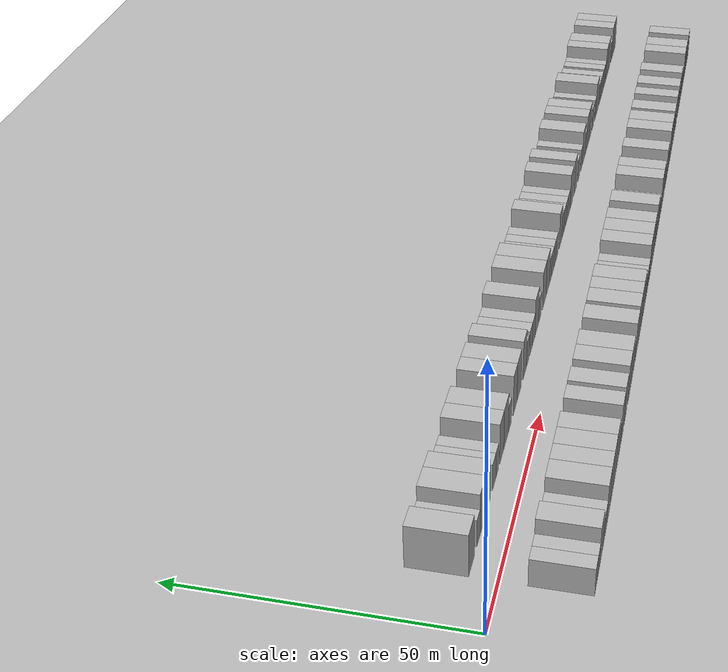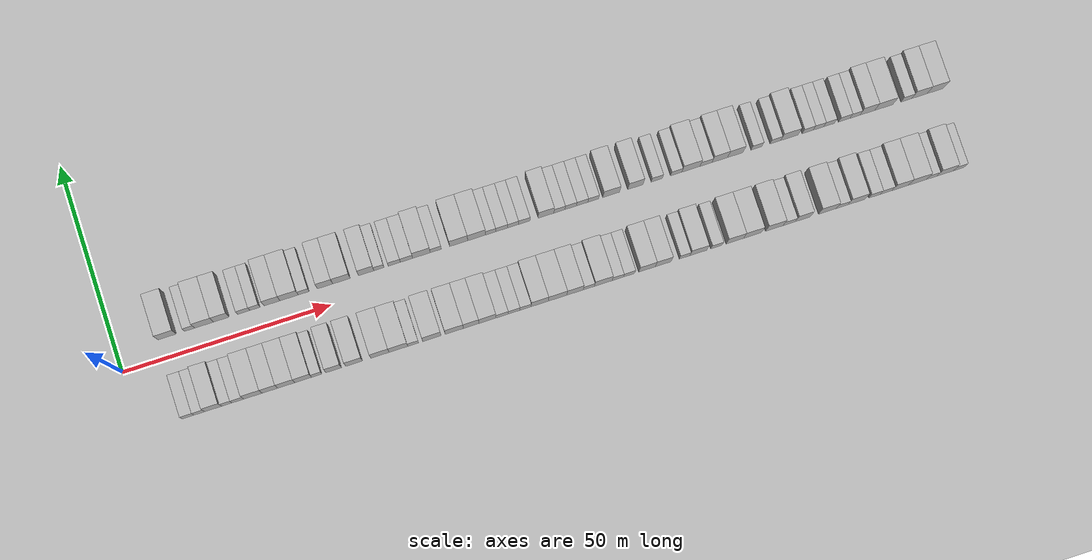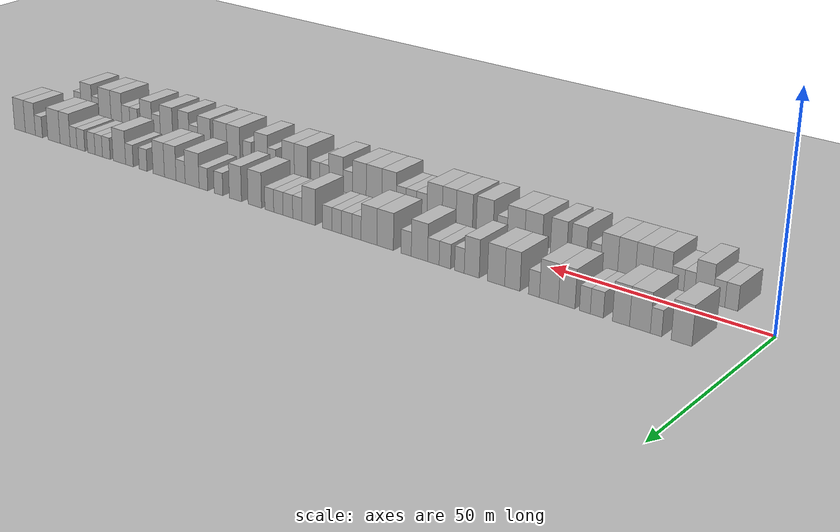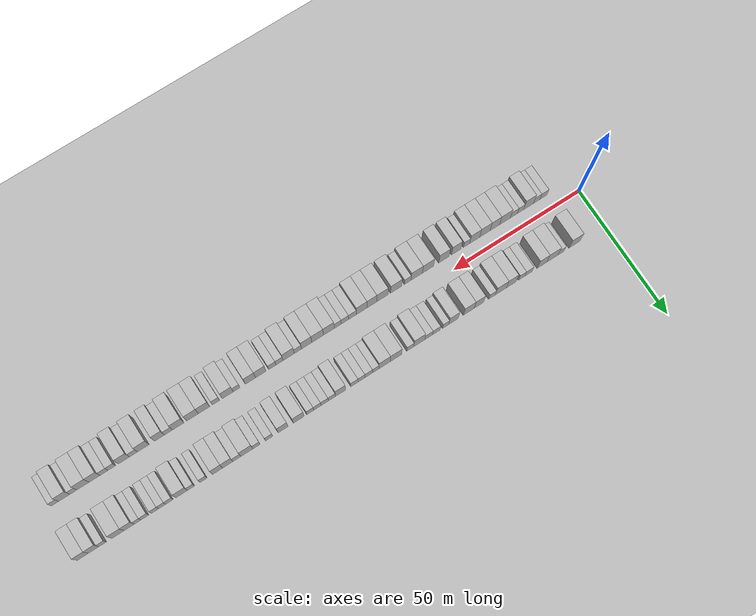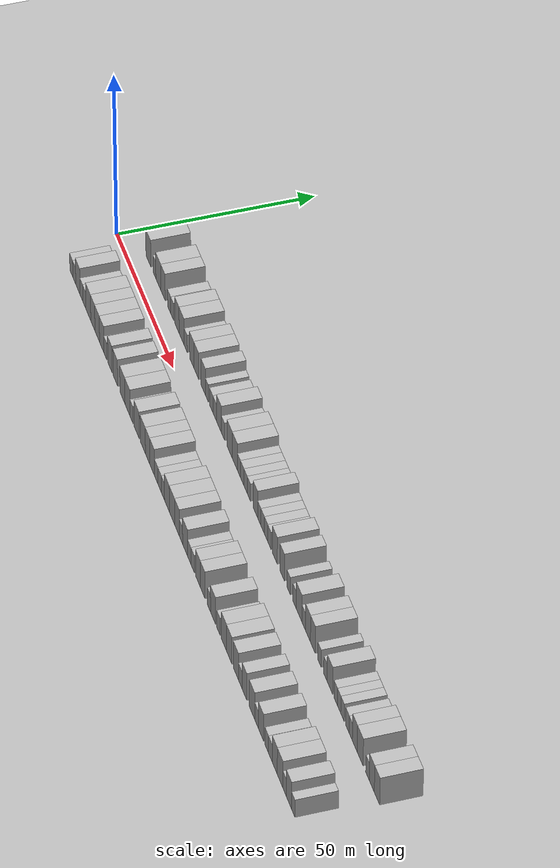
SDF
<?xml version="1.0" encoding="utf-8"?>

<sdf version="1.6">

   <world name="default">

      <gui fullscreen="0">

         <camera name="user_camera">

            <pose>-15 0 4.57585 0 0 0</pose>

            <view_controller>orbit</view_controller>

         </camera>

      </gui>

      <scene>

         <sky>

           <clouds>

             <speed>12</speed>

           </clouds>

         </sky>

         <ambient>0.4 0.4 0.4 1</ambient>

         <background>0.7 0.7 0.7 1</background>

         <shadows>1</shadows>

      </scene>

      <gravity>0 0 -9.8066</gravity>

      <magnetic_field>6e-06 2.3e-05 -4.2e-05</magnetic_field>

      <physics default="0" name="default_physics" type="ode">

         <ode>

            <solver>

               <type>quick</type>

               <iters>10</iters>

               <sor>1.0</sor>

               <use_dynamic_moi_rescaling>0</use_dynamic_moi_rescaling>

            </solver>

            <constraints>

               <cfm>0</cfm>

               <erp>0.2</erp>

               <contact_max_correcting_vel>100</contact_max_correcting_vel>

               <contact_surface_layer>0.001</contact_surface_layer>

            </constraints>

         </ode>

         <max_step_size>0.004</max_step_size>

         <real_time_factor>1</real_time_factor>

         <real_time_update_rate>250</real_time_update_rate>

      </physics>

      <light name="sun" type="directional">

         <cast_shadows>1</cast_shadows>

         <pose>0 0 10 0 0 0</pose>

         <diffuse>0.8 0.8 0.8 1</diffuse>

         <specular>0.2 0.2 0.2 1</specular>

         <attenuation>

            <range>1000</range>

            <constant>0.9</constant>

            <linear>0.01</linear>

            <quadratic>0.001</quadratic>

         </attenuation>

         <direction>-0.5 0.1 -0.9</direction>

      </light>

      <include>

         <name>ground_plane_1</name>

         <uri>model://HANNAS_ground_plane</uri>

         <pose>0 0 0  0 0 0</pose>

      </include>

      <include>

         <name>ground_plane_2</name>

         <uri>model://HANNAS_ground_plane</uri>

         <pose>100 0 0  0 0 0</pose>

      </include>

      <model name="building_1">

         <static>1</static>

         <pose frame="">12.1707 9.5000 0 0.000000 0.000000 1.570796</pose>

         <link name="link">

            <pose frame="">0 0 4.50 0 0 0</pose>

            <collision name="collision">

               <geometry>

                  <box>

                     <size>10.0000 4.3413 9.0000</size>

                  </box>

               </geometry>

               <max_contacts>10</max_contacts>

               <surface>

                  <contact>

                     <ode/>

                  </contact>

                  <bounce/>

                  <friction>

                     <torsional>

                        <ode/>

                     </torsional>

                     <ode/>

                  </friction>

               </surface>

            </collision>

            <visual name="visual">

               <cast_shadows>0</cast_shadows>

               <geometry>

                  <box>

                     <size>10.0000 4.3413 9.0000</size>

                  </box>

               </geometry>

               <material>

                  <script>

                     <uri>model://HANNAS_wall/materials/scripts</uri>

                     <uri>model://HANNAS_wall/materials/textures</uri>

                     <name>vrc/HANNAS_wall</name>

                  </script>

               </material>

            </visual>

            <self_collide>0</self_collide>

            <enable_wind>0</enable_wind>

            <kinematic>0</kinematic>

         </link>

      </model>

      <model name="building_2">

         <static>1</static>

         <pose frame="">17.5541 9.5000 0 0.000000 0.000000 1.570796</pose>

         <link name="link">

            <pose frame="">0 0 3.00 0 0 0</pose>

            <collision name="collision">

               <geometry>

                  <box>

                     <size>10.0000 2.4256 6.0000</size>

                  </box>

               </geometry>

               <max_contacts>10</max_contacts>

               <surface>

                  <contact>

                     <ode/>

                  </contact>

                  <bounce/>

                  <friction>

                     <torsional>

                        <ode/>

                     </torsional>

                     <ode/>

                  </friction>

               </surface>

            </collision>

            <visual name="visual">

               <cast_shadows>0</cast_shadows>

               <geometry>

                  <box>

                     <size>10.0000 2.4256 6.0000</size>

                  </box>

               </geometry>

               <material>

                  <script>

                     <uri>model://HANNAS_wall/materials/scripts</uri>

                     <uri>model://HANNAS_wall/materials/textures</uri>

                     <name>vrc/HANNAS_wall</name>

                  </script>

               </material>

            </visual>

            <self_collide>0</self_collide>

            <enable_wind>0</enable_wind>

            <kinematic>0</kinematic>

         </link>

      </model>

      <model name="building_3">

         <static>1</static>

         <pose frame="">21.0148 9.5000 0 0.000000 0.000000 1.570796</pose>

         <link name="link">

            <pose frame="">0 0 4.50 0 0 0</pose>

            <collision name="collision">

               <geometry>

                  <box>

                     <size>10.0000 4.4958 9.0000</size>

                  </box>

               </geometry>

               <max_contacts>10</max_contacts>

               <surface>

                  <contact>

                     <ode/>

                  </contact>

                  <bounce/>

                  <friction>

                     <torsional>

                        <ode/>

                     </torsional>

                     <ode/>

                  </friction>

               </surface>

            </collision>

            <visual name="visual">

               <cast_shadows>0</cast_shadows>

               <geometry>

                  <box>

                     <size>10.0000 4.4958 9.0000</size>

                  </box>

               </geometry>

               <material>

                  <script>

                     <uri>model://HANNAS_wall/materials/scripts</uri>

                     <uri>model://HANNAS_wall/materials/textures</uri>

                     <name>vrc/HANNAS_wall</name>

                  </script>

               </material>

            </visual>

            <self_collide>0</self_collide>

            <enable_wind>0</enable_wind>

            <kinematic>0</kinematic>

         </link>

      </model>

      <model name="building_4">

         <static>1</static>

         <pose frame="">25.1344 9.5000 0 0.000000 0.000000 1.570796</pose>

         <link name="link">

            <pose frame="">0 0 4.50 0 0 0</pose>

            <collision name="collision">

               <geometry>

                  <box>

                     <size>10.0000 3.7433 9.0000</size>

                  </box>

               </geometry>

               <max_contacts>10</max_contacts>

               <surface>

                  <contact>

                     <ode/>

                  </contact>

                  <bounce/>

                  <friction>

                     <torsional>

                        <ode/>

                     </torsional>

                     <ode/>

                  </friction>

               </surface>

            </collision>

            <visual name="visual">

               <cast_shadows>0</cast_shadows>

               <geometry>

                  <box>

                     <size>10.0000 3.7433 9.0000</size>

                  </box>

               </geometry>

               <material>

                  <script>

                     <uri>model://HANNAS_wall/materials/scripts</uri>

                     <uri>model://HANNAS_wall/materials/textures</uri>

                     <name>vrc/HANNAS_wall</name>

                  </script>

               </material>

            </visual>

            <self_collide>0</self_collide>

            <enable_wind>0</enable_wind>

            <kinematic>0</kinematic>

         </link>

      </model>

      <model name="building_5">

         <static>1</static>

         <pose frame="">30.4679 9.5000 0 0.000000 0.000000 1.570796</pose>

         <link name="link">

            <pose frame="">0 0 3.00 0 0 0</pose>

            <collision name="collision">

               <geometry>

                  <box>

                     <size>10.0000 2.9237 6.0000</size>

                  </box>

               </geometry>

               <max_contacts>10</max_contacts>

               <surface>

                  <contact>

                     <ode/>

                  </contact>

                  <bounce/>

                  <friction>

                     <torsional>

                        <ode/>

                     </torsional>

                     <ode/>

                  </friction>

               </surface>

            </collision>

            <visual name="visual">

               <cast_shadows>0</cast_shadows>

               <geometry>

                  <box>

                     <size>10.0000 2.9237 6.0000</size>

                  </box>

               </geometry>

               <material>

                  <script>

                     <uri>model://HANNAS_wall/materials/scripts</uri>

                     <uri>model://HANNAS_wall/materials/textures</uri>

                     <name>vrc/HANNAS_wall</name>

                  </script>

               </material>

            </visual>

            <self_collide>0</self_collide>

            <enable_wind>0</enable_wind>

            <kinematic>0</kinematic>

         </link>

      </model>

      <model name="building_6">

         <static>1</static>

         <pose frame="">33.1570 9.5000 0 0.000000 0.000000 1.570796</pose>

         <link name="link">

            <pose frame="">0 0 3.00 0 0 0</pose>

            <collision name="collision">

               <geometry>

                  <box>

                     <size>10.0000 2.4545 6.0000</size>

                  </box>

               </geometry>

               <max_contacts>10</max_contacts>

               <surface>

                  <contact>

                     <ode/>

                  </contact>

                  <bounce/>

                  <friction>

                     <torsional>

                        <ode/>

                     </torsional>

                     <ode/>

                  </friction>

               </surface>

            </collision>

            <visual name="visual">

               <cast_shadows>0</cast_shadows>

               <geometry>

                  <box>

                     <size>10.0000 2.4545 6.0000</size>

                  </box>

               </geometry>

               <material>

                  <script>

                     <uri>model://HANNAS_wall/materials/scripts</uri>

                     <uri>model://HANNAS_wall/materials/textures</uri>

                     <name>vrc/HANNAS_wall</name>

                  </script>

               </material>

            </visual>

            <self_collide>0</self_collide>

            <enable_wind>0</enable_wind>

            <kinematic>0</kinematic>

         </link>

      </model>

      <model name="building_7">

         <static>1</static>

         <pose frame="">37.2861 9.5000 0 0.000000 0.000000 1.570796</pose>

         <link name="link">

            <pose frame="">0 0 4.50 0 0 0</pose>

            <collision name="collision">

               <geometry>

                  <box>

                     <size>10.0000 3.8037 9.0000</size>

                  </box>

               </geometry>

               <max_contacts>10</max_contacts>

               <surface>

                  <contact>

                     <ode/>

                  </contact>

                  <bounce/>

                  <friction>

                     <torsional>

                        <ode/>

                     </torsional>

                     <ode/>

                  </friction>

               </surface>

            </collision>

            <visual name="visual">

               <cast_shadows>0</cast_shadows>

               <geometry>

                  <box>

                     <size>10.0000 3.8037 9.0000</size>

                  </box>

               </geometry>

               <material>

                  <script>

                     <uri>model://HANNAS_wall/materials/scripts</uri>

                     <uri>model://HANNAS_wall/materials/textures</uri>

                     <name>vrc/HANNAS_wall</name>

                  </script>

               </material>

            </visual>

            <self_collide>0</self_collide>

            <enable_wind>0</enable_wind>

            <kinematic>0</kinematic>

         </link>

      </model>

      <model name="building_8">

         <static>1</static>

         <pose frame="">41.3800 9.5000 0 0.000000 0.000000 1.570796</pose>

         <link name="link">

            <pose frame="">0 0 4.50 0 0 0</pose>

            <collision name="collision">

               <geometry>

                  <box>

                     <size>10.0000 4.3842 9.0000</size>

                  </box>

               </geometry>

               <max_contacts>10</max_contacts>

               <surface>

                  <contact>

                     <ode/>

                  </contact>

                  <bounce/>

                  <friction>

                     <torsional>

                        <ode/>

                     </torsional>

                     <ode/>

                  </friction>

               </surface>

            </collision>

            <visual name="visual">

               <cast_shadows>0</cast_shadows>

               <geometry>

                  <box>

                     <size>10.0000 4.3842 9.0000</size>

                  </box>

               </geometry>

               <material>

                  <script>

                     <uri>model://HANNAS_wall/materials/scripts</uri>

                     <uri>model://HANNAS_wall/materials/textures</uri>

                     <name>vrc/HANNAS_wall</name>

                  </script>

               </material>

            </visual>

            <self_collide>0</self_collide>

            <enable_wind>0</enable_wind>

            <kinematic>0</kinematic>

         </link>

      </model>

      <model name="building_9">

         <static>1</static>

         <pose frame="">44.8732 9.5000 0 0.000000 0.000000 1.570796</pose>

         <link name="link">

            <pose frame="">0 0 3.00 0 0 0</pose>

            <collision name="collision">

               <geometry>

                  <box>

                     <size>10.0000 2.6022 6.0000</size>

                  </box>

               </geometry>

               <max_contacts>10</max_contacts>

               <surface>

                  <contact>

                     <ode/>

                  </contact>

                  <bounce/>

                  <friction>

                     <torsional>

                        <ode/>

                     </torsional>

                     <ode/>

                  </friction>

               </surface>

            </collision>

            <visual name="visual">

               <cast_shadows>0</cast_shadows>

               <geometry>

                  <box>

                     <size>10.0000 2.6022 6.0000</size>

                  </box>

               </geometry>

               <material>

                  <script>

                     <uri>model://HANNAS_wall/materials/scripts</uri>

                     <uri>model://HANNAS_wall/materials/textures</uri>

                     <name>vrc/HANNAS_wall</name>

                  </script>

               </material>

            </visual>

            <self_collide>0</self_collide>

            <enable_wind>0</enable_wind>

            <kinematic>0</kinematic>

         </link>

      </model>

      <model name="building_10">

         <static>1</static>

         <pose frame="">50.0068 9.5000 0 0.000000 0.000000 1.570796</pose>

         <link name="link">

            <pose frame="">0 0 4.50 0 0 0</pose>

            <collision name="collision">

               <geometry>

                  <box>

                     <size>10.0000 3.6650 9.0000</size>

                  </box>

               </geometry>

               <max_contacts>10</max_contacts>

               <surface>

                  <contact>

                     <ode/>

                  </contact>

                  <bounce/>

                  <friction>

                     <torsional>

                        <ode/>

                     </torsional>

                     <ode/>

                  </friction>

               </surface>

            </collision>

            <visual name="visual">

               <cast_shadows>0</cast_shadows>

               <geometry>

                  <box>

                     <size>10.0000 3.6650 9.0000</size>

                  </box>

               </geometry>

               <material>

                  <script>

                     <uri>model://HANNAS_wall/materials/scripts</uri>

                     <uri>model://HANNAS_wall/materials/textures</uri>

                     <name>vrc/HANNAS_wall</name>

                  </script>

               </material>

            </visual>

            <self_collide>0</self_collide>

            <enable_wind>0</enable_wind>

            <kinematic>0</kinematic>

         </link>

      </model>

      <model name="building_11">

         <static>1</static>

         <pose frame="">53.9409 9.5000 0 0.000000 0.000000 1.570796</pose>

         <link name="link">

            <pose frame="">0 0 4.50 0 0 0</pose>

            <collision name="collision">

               <geometry>

                  <box>

                     <size>10.0000 4.2031 9.0000</size>

                  </box>

               </geometry>

               <max_contacts>10</max_contacts>

               <surface>

                  <contact>

                     <ode/>

                  </contact>

                  <bounce/>

                  <friction>

                     <torsional>

                        <ode/>

                     </torsional>

                     <ode/>

                  </friction>

               </surface>

            </collision>

            <visual name="visual">

               <cast_shadows>0</cast_shadows>

               <geometry>

                  <box>

                     <size>10.0000 4.2031 9.0000</size>

                  </box>

               </geometry>

               <material>

                  <script>

                     <uri>model://HANNAS_wall/materials/scripts</uri>

                     <uri>model://HANNAS_wall/materials/textures</uri>

                     <name>vrc/HANNAS_wall</name>

                  </script>

               </material>

            </visual>

            <self_collide>0</self_collide>

            <enable_wind>0</enable_wind>

            <kinematic>0</kinematic>

         </link>

      </model>

      <model name="building_12">

         <static>1</static>

         <pose frame="">59.8919 9.5000 0 0.000000 0.000000 1.570796</pose>

         <link name="link">

            <pose frame="">0 0 4.50 0 0 0</pose>

            <collision name="collision">

               <geometry>

                  <box>

                     <size>10.0000 3.6989 9.0000</size>

                  </box>

               </geometry>

               <max_contacts>10</max_contacts>

               <surface>

                  <contact>

                     <ode/>

                  </contact>

                  <bounce/>

                  <friction>

                     <torsional>

                        <ode/>

                     </torsional>

                     <ode/>

                  </friction>

               </surface>

            </collision>

            <visual name="visual">

               <cast_shadows>0</cast_shadows>

               <geometry>

                  <box>

                     <size>10.0000 3.6989 9.0000</size>

                  </box>

               </geometry>

               <material>

                  <script>

                     <uri>model://HANNAS_wall/materials/scripts</uri>

                     <uri>model://HANNAS_wall/materials/textures</uri>

                     <name>vrc/HANNAS_wall</name>

                  </script>

               </material>

            </visual>

            <self_collide>0</self_collide>

            <enable_wind>0</enable_wind>

            <kinematic>0</kinematic>

         </link>

      </model>

      <model name="building_13">

         <static>1</static>

         <pose frame="">62.9533 9.5000 0 0.000000 0.000000 1.570796</pose>

         <link name="link">

            <pose frame="">0 0 3.00 0 0 0</pose>

            <collision name="collision">

               <geometry>

                  <box>

                     <size>10.0000 2.4239 6.0000</size>

                  </box>

               </geometry>

               <max_contacts>10</max_contacts>

               <surface>

                  <contact>

                     <ode/>

                  </contact>

                  <bounce/>

                  <friction>

                     <torsional>

                        <ode/>

                     </torsional>

                     <ode/>

                  </friction>

               </surface>

            </collision>

            <visual name="visual">

               <cast_shadows>0</cast_shadows>

               <geometry>

                  <box>

                     <size>10.0000 2.4239 6.0000</size>

                  </box>

               </geometry>

               <material>

                  <script>

                     <uri>model://HANNAS_wall/materials/scripts</uri>

                     <uri>model://HANNAS_wall/materials/textures</uri>

                     <name>vrc/HANNAS_wall</name>

                  </script>

               </material>

            </visual>

            <self_collide>0</self_collide>

            <enable_wind>0</enable_wind>

            <kinematic>0</kinematic>

         </link>

      </model>

      <model name="building_14">

         <static>1</static>

         <pose frame="">66.6167 9.5000 0 0.000000 0.000000 1.570796</pose>

         <link name="link">

            <pose frame="">0 0 3.00 0 0 0</pose>

            <collision name="collision">

               <geometry>

                  <box>

                     <size>10.0000 2.9030 6.0000</size>

                  </box>

               </geometry>

               <max_contacts>10</max_contacts>

               <surface>

                  <contact>

                     <ode/>

                  </contact>

                  <bounce/>

                  <friction>

                     <torsional>

                        <ode/>

                     </torsional>

                     <ode/>

                  </friction>

               </surface>

            </collision>

            <visual name="visual">

               <cast_shadows>0</cast_shadows>

               <geometry>

                  <box>

                     <size>10.0000 2.9030 6.0000</size>

                  </box>

               </geometry>

               <material>

                  <script>

                     <uri>model://HANNAS_wall/materials/scripts</uri>

                     <uri>model://HANNAS_wall/materials/textures</uri>

                     <name>vrc/HANNAS_wall</name>

                  </script>

               </material>

            </visual>

            <self_collide>0</self_collide>

            <enable_wind>0</enable_wind>

            <kinematic>0</kinematic>

         </link>

      </model>

      <model name="building_15">

         <static>1</static>

         <pose frame="">69.5515 9.5000 0 0.000000 0.000000 1.570796</pose>

         <link name="link">

            <pose frame="">0 0 3.00 0 0 0</pose>

            <collision name="collision">

               <geometry>

                  <box>

                     <size>10.0000 2.9666 6.0000</size>

                  </box>

               </geometry>

               <max_contacts>10</max_contacts>

               <surface>

                  <contact>

                     <ode/>

                  </contact>

                  <bounce/>

                  <friction>

                     <torsional>

                        <ode/>

                     </torsional>

                     <ode/>

                  </friction>

               </surface>

            </collision>

            <visual name="visual">

               <cast_shadows>0</cast_shadows>

               <geometry>

                  <box>

                     <size>10.0000 2.9666 6.0000</size>

                  </box>

               </geometry>

               <material>

                  <script>

                     <uri>model://HANNAS_wall/materials/scripts</uri>

                     <uri>model://HANNAS_wall/materials/textures</uri>

                     <name>vrc/HANNAS_wall</name>

                  </script>

               </material>

            </visual>

            <self_collide>0</self_collide>

            <enable_wind>0</enable_wind>

            <kinematic>0</kinematic>

         </link>

      </model>

      <model name="building_16">

         <static>1</static>

         <pose frame="">73.1514 9.5000 0 0.000000 0.000000 1.570796</pose>

         <link name="link">

            <pose frame="">0 0 4.50 0 0 0</pose>

            <collision name="collision">

               <geometry>

                  <box>

                     <size>10.0000 4.2332 9.0000</size>

                  </box>

               </geometry>

               <max_contacts>10</max_contacts>

               <surface>

                  <contact>

                     <ode/>

                  </contact>

                  <bounce/>

                  <friction>

                     <torsional>

                        <ode/>

                     </torsional>

                     <ode/>

                  </friction>

               </surface>

            </collision>

            <visual name="visual">

               <cast_shadows>0</cast_shadows>

               <geometry>

                  <box>

                     <size>10.0000 4.2332 9.0000</size>

                  </box>

               </geometry>

               <material>

                  <script>

                     <uri>model://HANNAS_wall/materials/scripts</uri>

                     <uri>model://HANNAS_wall/materials/textures</uri>

                     <name>vrc/HANNAS_wall</name>

                  </script>

               </material>

            </visual>

            <self_collide>0</self_collide>

            <enable_wind>0</enable_wind>

            <kinematic>0</kinematic>

         </link>

      </model>

      <model name="building_17">

         <static>1</static>

         <pose frame="">76.6122 9.5000 0 0.000000 0.000000 1.570796</pose>

         <link name="link">

            <pose frame="">0 0 3.00 0 0 0</pose>

            <collision name="collision">

               <geometry>

                  <box>

                     <size>10.0000 2.6884 6.0000</size>

                  </box>

               </geometry>

               <max_contacts>10</max_contacts>

               <surface>

                  <contact>

                     <ode/>

                  </contact>

                  <bounce/>

                  <friction>

                     <torsional>

                        <ode/>

                     </torsional>

                     <ode/>

                  </friction>

               </surface>

            </collision>

            <visual name="visual">

               <cast_shadows>0</cast_shadows>

               <geometry>

                  <box>

                     <size>10.0000 2.6884 6.0000</size>

                  </box>

               </geometry>

               <material>

                  <script>

                     <uri>model://HANNAS_wall/materials/scripts</uri>

                     <uri>model://HANNAS_wall/materials/textures</uri>

                     <name>vrc/HANNAS_wall</name>

                  </script>

               </material>

            </visual>

            <self_collide>0</self_collide>

            <enable_wind>0</enable_wind>

            <kinematic>0</kinematic>

         </link>

      </model>

      <model name="building_18">

         <static>1</static>

         <pose frame="">82.1351 9.5000 0 0.000000 0.000000 1.570796</pose>

         <link name="link">

            <pose frame="">0 0 4.50 0 0 0</pose>

            <collision name="collision">

               <geometry>

                  <box>

                     <size>10.0000 4.3573 9.0000</size>

                  </box>

               </geometry>

               <max_contacts>10</max_contacts>

               <surface>

                  <contact>

                     <ode/>

                  </contact>

                  <bounce/>

                  <friction>

                     <torsional>

                        <ode/>

                     </torsional>

                     <ode/>

                  </friction>

               </surface>

            </collision>

            <visual name="visual">

               <cast_shadows>0</cast_shadows>

               <geometry>

                  <box>

                     <size>10.0000 4.3573 9.0000</size>

                  </box>

               </geometry>

               <material>

                  <script>

                     <uri>model://HANNAS_wall/materials/scripts</uri>

                     <uri>model://HANNAS_wall/materials/textures</uri>

                     <name>vrc/HANNAS_wall</name>

                  </script>

               </material>

            </visual>

            <self_collide>0</self_collide>

            <enable_wind>0</enable_wind>

            <kinematic>0</kinematic>

         </link>

      </model>

      <model name="building_19">

         <static>1</static>

         <pose frame="">86.4716 9.5000 0 0.000000 0.000000 1.570796</pose>

         <link name="link">

            <pose frame="">0 0 4.50 0 0 0</pose>

            <collision name="collision">

               <geometry>

                  <box>

                     <size>10.0000 4.3158 9.0000</size>

                  </box>

               </geometry>

               <max_contacts>10</max_contacts>

               <surface>

                  <contact>

                     <ode/>

                  </contact>

                  <bounce/>

                  <friction>

                     <torsional>

                        <ode/>

                     </torsional>

                     <ode/>

                  </friction>

               </surface>

            </collision>

            <visual name="visual">

               <cast_shadows>0</cast_shadows>

               <geometry>

                  <box>

                     <size>10.0000 4.3158 9.0000</size>

                  </box>

               </geometry>

               <material>

                  <script>

                     <uri>model://HANNAS_wall/materials/scripts</uri>

                     <uri>model://HANNAS_wall/materials/textures</uri>

                     <name>vrc/HANNAS_wall</name>

                  </script>

               </material>

            </visual>

            <self_collide>0</self_collide>

            <enable_wind>0</enable_wind>

            <kinematic>0</kinematic>

         </link>

      </model>

      <model name="building_20">

         <static>1</static>

         <pose frame="">89.8686 9.5000 0 0.000000 0.000000 1.570796</pose>

         <link name="link">

            <pose frame="">0 0 3.00 0 0 0</pose>

            <collision name="collision">

               <geometry>

                  <box>

                     <size>10.0000 2.4782 6.0000</size>

                  </box>

               </geometry>

               <max_contacts>10</max_contacts>

               <surface>

                  <contact>

                     <ode/>

                  </contact>

                  <bounce/>

                  <friction>

                     <torsional>

                        <ode/>

                     </torsional>

                     <ode/>

                  </friction>

               </surface>

            </collision>

            <visual name="visual">

               <cast_shadows>0</cast_shadows>

               <geometry>

                  <box>

                     <size>10.0000 2.4782 6.0000</size>

                  </box>

               </geometry>

               <material>

                  <script>

                     <uri>model://HANNAS_wall/materials/scripts</uri>

                     <uri>model://HANNAS_wall/materials/textures</uri>

                     <name>vrc/HANNAS_wall</name>

                  </script>

               </material>

            </visual>

            <self_collide>0</self_collide>

            <enable_wind>0</enable_wind>

            <kinematic>0</kinematic>

         </link>

      </model>

      <model name="building_21">

         <static>1</static>

         <pose frame="">92.5483 9.5000 0 0.000000 0.000000 1.570796</pose>

         <link name="link">

            <pose frame="">0 0 3.00 0 0 0</pose>

            <collision name="collision">

               <geometry>

                  <box>

                     <size>10.0000 2.8812 6.0000</size>

                  </box>

               </geometry>

               <max_contacts>10</max_contacts>

               <surface>

                  <contact>

                     <ode/>

                  </contact>

                  <bounce/>

                  <friction>

                     <torsional>

                        <ode/>

                     </torsional>

                     <ode/>

                  </friction>

               </surface>

            </collision>

            <visual name="visual">

               <cast_shadows>0</cast_shadows>

               <geometry>

                  <box>

                     <size>10.0000 2.8812 6.0000</size>

                  </box>

               </geometry>

               <material>

                  <script>

                     <uri>model://HANNAS_wall/materials/scripts</uri>

                     <uri>model://HANNAS_wall/materials/textures</uri>

                     <name>vrc/HANNAS_wall</name>

                  </script>

               </material>

            </visual>

            <self_collide>0</self_collide>

            <enable_wind>0</enable_wind>

            <kinematic>0</kinematic>

         </link>

      </model>

      <model name="building_22">

         <static>1</static>

         <pose frame="">95.3012 9.5000 0 0.000000 0.000000 1.570796</pose>

         <link name="link">

            <pose frame="">0 0 3.00 0 0 0</pose>

            <collision name="collision">

               <geometry>

                  <box>

                     <size>10.0000 2.6247 6.0000</size>

                  </box>

               </geometry>

               <max_contacts>10</max_contacts>

               <surface>

                  <contact>

                     <ode/>

                  </contact>

                  <bounce/>

                  <friction>

                     <torsional>

                        <ode/>

                     </torsional>

                     <ode/>

                  </friction>

               </surface>

            </collision>

            <visual name="visual">

               <cast_shadows>0</cast_shadows>

               <geometry>

                  <box>

                     <size>10.0000 2.6247 6.0000</size>

                  </box>

               </geometry>

               <material>

                  <script>

                     <uri>model://HANNAS_wall/materials/scripts</uri>

                     <uri>model://HANNAS_wall/materials/textures</uri>

                     <name>vrc/HANNAS_wall</name>

                  </script>

               </material>

            </visual>

            <self_collide>0</self_collide>

            <enable_wind>0</enable_wind>

            <kinematic>0</kinematic>

         </link>

      </model>

      <model name="building_23">

         <static>1</static>

         <pose frame="">97.9914 9.5000 0 0.000000 0.000000 1.570796</pose>

         <link name="link">

            <pose frame="">0 0 3.00 0 0 0</pose>

            <collision name="collision">

               <geometry>

                  <box>

                     <size>10.0000 2.7557 6.0000</size>

                  </box>

               </geometry>

               <max_contacts>10</max_contacts>

               <surface>

                  <contact>

                     <ode/>

                  </contact>

                  <bounce/>

                  <friction>

                     <torsional>

                        <ode/>

                     </torsional>

                     <ode/>

                  </friction>

               </surface>

            </collision>

            <visual name="visual">

               <cast_shadows>0</cast_shadows>

               <geometry>

                  <box>

                     <size>10.0000 2.7557 6.0000</size>

                  </box>

               </geometry>

               <material>

                  <script>

                     <uri>model://HANNAS_wall/materials/scripts</uri>

                     <uri>model://HANNAS_wall/materials/textures</uri>

                     <name>vrc/HANNAS_wall</name>

                  </script>

               </material>

            </visual>

            <self_collide>0</self_collide>

            <enable_wind>0</enable_wind>

            <kinematic>0</kinematic>

         </link>

      </model>

      <model name="building_24">

         <static>1</static>

         <pose frame="">103.2689 9.5000 0 0.000000 0.000000 1.570796</pose>

         <link name="link">

            <pose frame="">0 0 4.50 0 0 0</pose>

            <collision name="collision">

               <geometry>

                  <box>

                     <size>10.0000 3.7992 9.0000</size>

                  </box>

               </geometry>

               <max_contacts>10</max_contacts>

               <surface>

                  <contact>

                     <ode/>

                  </contact>

                  <bounce/>

                  <friction>

                     <torsional>

                        <ode/>

                     </torsional>

                     <ode/>

                  </friction>

               </surface>

            </collision>

            <visual name="visual">

               <cast_shadows>0</cast_shadows>

               <geometry>

                  <box>

                     <size>10.0000 3.7992 9.0000</size>

                  </box>

               </geometry>

               <material>

                  <script>

                     <uri>model://HANNAS_wall/materials/scripts</uri>

                     <uri>model://HANNAS_wall/materials/textures</uri>

                     <name>vrc/HANNAS_wall</name>

                  </script>

               </material>

            </visual>

            <self_collide>0</self_collide>

            <enable_wind>0</enable_wind>

            <kinematic>0</kinematic>

         </link>

      </model>

      <model name="building_25">

         <static>1</static>

         <pose frame="">106.5121 9.5000 0 0.000000 0.000000 1.570796</pose>

         <link name="link">

            <pose frame="">0 0 3.00 0 0 0</pose>

            <collision name="collision">

               <geometry>

                  <box>

                     <size>10.0000 2.6872 6.0000</size>

                  </box>

               </geometry>

               <max_contacts>10</max_contacts>

               <surface>

                  <contact>

                     <ode/>

                  </contact>

                  <bounce/>

                  <friction>

                     <torsional>

                        <ode/>

                     </torsional>

                     <ode/>

                  </friction>

               </surface>

            </collision>

            <visual name="visual">

               <cast_shadows>0</cast_shadows>

               <geometry>

                  <box>

                     <size>10.0000 2.6872 6.0000</size>

                  </box>

               </geometry>

               <material>

                  <script>

                     <uri>model://HANNAS_wall/materials/scripts</uri>

                     <uri>model://HANNAS_wall/materials/textures</uri>

                     <name>vrc/HANNAS_wall</name>

                  </script>

               </material>

            </visual>

            <self_collide>0</self_collide>

            <enable_wind>0</enable_wind>

            <kinematic>0</kinematic>

         </link>

      </model>

      <model name="building_26">

         <static>1</static>

         <pose frame="">109.2533 9.5000 0 0.000000 0.000000 1.570796</pose>

         <link name="link">

            <pose frame="">0 0 3.00 0 0 0</pose>

            <collision name="collision">

               <geometry>

                  <box>

                     <size>10.0000 2.7952 6.0000</size>

                  </box>

               </geometry>

               <max_contacts>10</max_contacts>

               <surface>

                  <contact>

                     <ode/>

                  </contact>

                  <bounce/>

                  <friction>

                     <torsional>

                        <ode/>

                     </torsional>

                     <ode/>

                  </friction>

               </surface>

            </collision>

            <visual name="visual">

               <cast_shadows>0</cast_shadows>

               <geometry>

                  <box>

                     <size>10.0000 2.7952 6.0000</size>

                  </box>

               </geometry>

               <material>

                  <script>

                     <uri>model://HANNAS_wall/materials/scripts</uri>

                     <uri>model://HANNAS_wall/materials/textures</uri>

                     <name>vrc/HANNAS_wall</name>

                  </script>

               </material>

            </visual>

            <self_collide>0</self_collide>

            <enable_wind>0</enable_wind>

            <kinematic>0</kinematic>

         </link>

      </model>

      <model name="building_27">

         <static>1</static>

         <pose frame="">112.0326 9.5000 0 0.000000 0.000000 1.570796</pose>

         <link name="link">

            <pose frame="">0 0 3.00 0 0 0</pose>

            <collision name="collision">

               <geometry>

                  <box>

                     <size>10.0000 2.7635 6.0000</size>

                  </box>

               </geometry>

               <max_contacts>10</max_contacts>

               <surface>

                  <contact>

                     <ode/>

                  </contact>

                  <bounce/>

                  <friction>

                     <torsional>

                        <ode/>

                     </torsional>

                     <ode/>

                  </friction>

               </surface>

            </collision>

            <visual name="visual">

               <cast_shadows>0</cast_shadows>

               <geometry>

                  <box>

                     <size>10.0000 2.7635 6.0000</size>

                  </box>

               </geometry>

               <material>

                  <script>

                     <uri>model://HANNAS_wall/materials/scripts</uri>

                     <uri>model://HANNAS_wall/materials/textures</uri>

                     <name>vrc/HANNAS_wall</name>

                  </script>

               </material>

            </visual>

            <self_collide>0</self_collide>

            <enable_wind>0</enable_wind>

            <kinematic>0</kinematic>

         </link>

      </model>

      <model name="building_28">

         <static>1</static>

         <pose frame="">114.7255 9.5000 0 0.000000 0.000000 1.570796</pose>

         <link name="link">

            <pose frame="">0 0 3.00 0 0 0</pose>

            <collision name="collision">

               <geometry>

                  <box>

                     <size>10.0000 2.6223 6.0000</size>

                  </box>

               </geometry>

               <max_contacts>10</max_contacts>

               <surface>

                  <contact>

                     <ode/>

                  </contact>

                  <bounce/>

                  <friction>

                     <torsional>

                        <ode/>

                     </torsional>

                     <ode/>

                  </friction>

               </surface>

            </collision>

            <visual name="visual">

               <cast_shadows>0</cast_shadows>

               <geometry>

                  <box>

                     <size>10.0000 2.6223 6.0000</size>

                  </box>

               </geometry>

               <material>

                  <script>

                     <uri>model://HANNAS_wall/materials/scripts</uri>

                     <uri>model://HANNAS_wall/materials/textures</uri>

                     <name>vrc/HANNAS_wall</name>

                  </script>

               </material>

            </visual>

            <self_collide>0</self_collide>

            <enable_wind>0</enable_wind>

            <kinematic>0</kinematic>

         </link>

      </model>

      <model name="building_29">

         <static>1</static>

         <pose frame="">119.0576 9.5000 0 0.000000 0.000000 1.570796</pose>

         <link name="link">

            <pose frame="">0 0 4.50 0 0 0</pose>

            <collision name="collision">

               <geometry>

                  <box>

                     <size>10.0000 4.0419 9.0000</size>

                  </box>

               </geometry>

               <max_contacts>10</max_contacts>

               <surface>

                  <contact>

                     <ode/>

                  </contact>

                  <bounce/>

                  <friction>

                     <torsional>

                        <ode/>

                     </torsional>

                     <ode/>

                  </friction>

               </surface>

            </collision>

            <visual name="visual">

               <cast_shadows>0</cast_shadows>

               <geometry>

                  <box>

                     <size>10.0000 4.0419 9.0000</size>

                  </box>

               </geometry>

               <material>

                  <script>

                     <uri>model://HANNAS_wall/materials/scripts</uri>

                     <uri>model://HANNAS_wall/materials/textures</uri>

                     <name>vrc/HANNAS_wall</name>

                  </script>

               </material>

            </visual>

            <self_collide>0</self_collide>

            <enable_wind>0</enable_wind>

            <kinematic>0</kinematic>

         </link>

      </model>

      <model name="building_30">

         <static>1</static>

         <pose frame="">124.9301 9.5000 0 0.000000 0.000000 1.570796</pose>

         <link name="link">

            <pose frame="">0 0 4.50 0 0 0</pose>

            <collision name="collision">

               <geometry>

                  <box>

                     <size>10.0000 3.7030 9.0000</size>

                  </box>

               </geometry>

               <max_contacts>10</max_contacts>

               <surface>

                  <contact>

                     <ode/>

                  </contact>

                  <bounce/>

                  <friction>

                     <torsional>

                        <ode/>

                     </torsional>

                     <ode/>

                  </friction>

               </surface>

            </collision>

            <visual name="visual">

               <cast_shadows>0</cast_shadows>

               <geometry>

                  <box>

                     <size>10.0000 3.7030 9.0000</size>

                  </box>

               </geometry>

               <material>

                  <script>

                     <uri>model://HANNAS_wall/materials/scripts</uri>

                     <uri>model://HANNAS_wall/materials/textures</uri>

                     <name>vrc/HANNAS_wall</name>

                  </script>

               </material>

            </visual>

            <self_collide>0</self_collide>

            <enable_wind>0</enable_wind>

            <kinematic>0</kinematic>

         </link>

      </model>

      <model name="building_31">

         <static>1</static>

         <pose frame="">130.1375 9.5000 0 0.000000 0.000000 1.570796</pose>

         <link name="link">

            <pose frame="">0 0 3.00 0 0 0</pose>

            <collision name="collision">

               <geometry>

                  <box>

                     <size>10.0000 2.7120 6.0000</size>

                  </box>

               </geometry>

               <max_contacts>10</max_contacts>

               <surface>

                  <contact>

                     <ode/>

                  </contact>

                  <bounce/>

                  <friction>

                     <torsional>

                        <ode/>

                     </torsional>

                     <ode/>

                  </friction>

               </surface>

            </collision>

            <visual name="visual">

               <cast_shadows>0</cast_shadows>

               <geometry>

                  <box>

                     <size>10.0000 2.7120 6.0000</size>

                  </box>

               </geometry>

               <material>

                  <script>

                     <uri>model://HANNAS_wall/materials/scripts</uri>

                     <uri>model://HANNAS_wall/materials/textures</uri>

                     <name>vrc/HANNAS_wall</name>

                  </script>

               </material>

            </visual>

            <self_collide>0</self_collide>

            <enable_wind>0</enable_wind>

            <kinematic>0</kinematic>

         </link>

      </model>

      <model name="building_32">

         <static>1</static>

         <pose frame="">134.8519 9.5000 0 0.000000 0.000000 1.570796</pose>

         <link name="link">

            <pose frame="">0 0 3.00 0 0 0</pose>

            <collision name="collision">

               <geometry>

                  <box>

                     <size>10.0000 2.7168 6.0000</size>

                  </box>

               </geometry>

               <max_contacts>10</max_contacts>

               <surface>

                  <contact>

                     <ode/>

                  </contact>

                  <bounce/>

                  <friction>

                     <torsional>

                        <ode/>

                     </torsional>

                     <ode/>

                  </friction>

               </surface>

            </collision>

            <visual name="visual">

               <cast_shadows>0</cast_shadows>

               <geometry>

                  <box>

                     <size>10.0000 2.7168 6.0000</size>

                  </box>

               </geometry>

               <material>

                  <script>

                     <uri>model://HANNAS_wall/materials/scripts</uri>

                     <uri>model://HANNAS_wall/materials/textures</uri>

                     <name>vrc/HANNAS_wall</name>

                  </script>

               </material>

            </visual>

            <self_collide>0</self_collide>

            <enable_wind>0</enable_wind>

            <kinematic>0</kinematic>

         </link>

      </model>

      <model name="building_33">

         <static>1</static>

         <pose frame="">138.4363 9.5000 0 0.000000 0.000000 1.570796</pose>

         <link name="link">

            <pose frame="">0 0 4.50 0 0 0</pose>

            <collision name="collision">

               <geometry>

                  <box>

                     <size>10.0000 4.4521 9.0000</size>

                  </box>

               </geometry>

               <max_contacts>10</max_contacts>

               <surface>

                  <contact>

                     <ode/>

                  </contact>

                  <bounce/>

                  <friction>

                     <torsional>

                        <ode/>

                     </torsional>

                     <ode/>

                  </friction>

               </surface>

            </collision>

            <visual name="visual">

               <cast_shadows>0</cast_shadows>

               <geometry>

                  <box>

                     <size>10.0000 4.4521 9.0000</size>

                  </box>

               </geometry>

               <material>

                  <script>

                     <uri>model://HANNAS_wall/materials/scripts</uri>

                     <uri>model://HANNAS_wall/materials/textures</uri>

                     <name>vrc/HANNAS_wall</name>

                  </script>

               </material>

            </visual>

            <self_collide>0</self_collide>

            <enable_wind>0</enable_wind>

            <kinematic>0</kinematic>

         </link>

      </model>

      <model name="building_34">

         <static>1</static>

         <pose frame="">142.1245 9.5000 0 0.000000 0.000000 1.570796</pose>

         <link name="link">

            <pose frame="">0 0 3.00 0 0 0</pose>

            <collision name="collision">

               <geometry>

                  <box>

                     <size>10.0000 2.9242 6.0000</size>

                  </box>

               </geometry>

               <max_contacts>10</max_contacts>

               <surface>

                  <contact>

                     <ode/>

                  </contact>

                  <bounce/>

                  <friction>

                     <torsional>

                        <ode/>

                     </torsional>

                     <ode/>

                  </friction>

               </surface>

            </collision>

            <visual name="visual">

               <cast_shadows>0</cast_shadows>

               <geometry>

                  <box>

                     <size>10.0000 2.9242 6.0000</size>

                  </box>

               </geometry>

               <material>

                  <script>

                     <uri>model://HANNAS_wall/materials/scripts</uri>

                     <uri>model://HANNAS_wall/materials/textures</uri>

                     <name>vrc/HANNAS_wall</name>

                  </script>

               </material>

            </visual>

            <self_collide>0</self_collide>

            <enable_wind>0</enable_wind>

            <kinematic>0</kinematic>

         </link>

      </model>

      <model name="building_35">

         <static>1</static>

         <pose frame="">145.4801 9.5000 0 0.000000 0.000000 1.570796</pose>

         <link name="link">

            <pose frame="">0 0 4.50 0 0 0</pose>

            <collision name="collision">

               <geometry>

                  <box>

                     <size>10.0000 3.7871 9.0000</size>

                  </box>

               </geometry>

               <max_contacts>10</max_contacts>

               <surface>

                  <contact>

                     <ode/>

                  </contact>

                  <bounce/>

                  <friction>

                     <torsional>

                        <ode/>

                     </torsional>

                     <ode/>

                  </friction>

               </surface>

            </collision>

            <visual name="visual">

               <cast_shadows>0</cast_shadows>

               <geometry>

                  <box>

                     <size>10.0000 3.7871 9.0000</size>

                  </box>

               </geometry>

               <material>

                  <script>

                     <uri>model://HANNAS_wall/materials/scripts</uri>

                     <uri>model://HANNAS_wall/materials/textures</uri>

                     <name>vrc/HANNAS_wall</name>

                  </script>

               </material>

            </visual>

            <self_collide>0</self_collide>

            <enable_wind>0</enable_wind>

            <kinematic>0</kinematic>

         </link>

      </model>

      <model name="building_36">

         <static>1</static>

         <pose frame="">149.2452 9.5000 0 0.000000 0.000000 1.570796</pose>

         <link name="link">

            <pose frame="">0 0 4.50 0 0 0</pose>

            <collision name="collision">

               <geometry>

                  <box>

                     <size>10.0000 3.7432 9.0000</size>

                  </box>

               </geometry>

               <max_contacts>10</max_contacts>

               <surface>

                  <contact>

                     <ode/>

                  </contact>

                  <bounce/>

                  <friction>

                     <torsional>

                        <ode/>

                     </torsional>

                     <ode/>

                  </friction>

               </surface>

            </collision>

            <visual name="visual">

               <cast_shadows>0</cast_shadows>

               <geometry>

                  <box>

                     <size>10.0000 3.7432 9.0000</size>

                  </box>

               </geometry>

               <material>

                  <script>

                     <uri>model://HANNAS_wall/materials/scripts</uri>

                     <uri>model://HANNAS_wall/materials/textures</uri>

                     <name>vrc/HANNAS_wall</name>

                  </script>

               </material>

            </visual>

            <self_collide>0</self_collide>

            <enable_wind>0</enable_wind>

            <kinematic>0</kinematic>

         </link>

      </model>

      <model name="building_37">

         <static>1</static>

         <pose frame="">154.4334 9.5000 0 0.000000 0.000000 1.570796</pose>

         <link name="link">

            <pose frame="">0 0 3.00 0 0 0</pose>

            <collision name="collision">

               <geometry>

                  <box>

                     <size>10.0000 2.6331 6.0000</size>

                  </box>

               </geometry>

               <max_contacts>10</max_contacts>

               <surface>

                  <contact>

                     <ode/>

                  </contact>

                  <bounce/>

                  <friction>

                     <torsional>

                        <ode/>

                     </torsional>

                     <ode/>

                  </friction>

               </surface>

            </collision>

            <visual name="visual">

               <cast_shadows>0</cast_shadows>

               <geometry>

                  <box>

                     <size>10.0000 2.6331 6.0000</size>

                  </box>

               </geometry>

               <material>

                  <script>

                     <uri>model://HANNAS_wall/materials/scripts</uri>

                     <uri>model://HANNAS_wall/materials/textures</uri>

                     <name>vrc/HANNAS_wall</name>

                  </script>

               </material>

            </visual>

            <self_collide>0</self_collide>

            <enable_wind>0</enable_wind>

            <kinematic>0</kinematic>

         </link>

      </model>

      <model name="building_38">

         <static>1</static>

         <pose frame="">159.0408 9.5000 0 0.000000 0.000000 1.570796</pose>

         <link name="link">

            <pose frame="">0 0 3.00 0 0 0</pose>

            <collision name="collision">

               <geometry>

                  <box>

                     <size>10.0000 2.5816 6.0000</size>

                  </box>

               </geometry>

               <max_contacts>10</max_contacts>

               <surface>

                  <contact>

                     <ode/>

                  </contact>

                  <bounce/>

                  <friction>

                     <torsional>

                        <ode/>

                     </torsional>

                     <ode/>

                  </friction>

               </surface>

            </collision>

            <visual name="visual">

               <cast_shadows>0</cast_shadows>

               <geometry>

                  <box>

                     <size>10.0000 2.5816 6.0000</size>

                  </box>

               </geometry>

               <material>

                  <script>

                     <uri>model://HANNAS_wall/materials/scripts</uri>

                     <uri>model://HANNAS_wall/materials/textures</uri>

                     <name>vrc/HANNAS_wall</name>

                  </script>

               </material>

            </visual>

            <self_collide>0</self_collide>

            <enable_wind>0</enable_wind>

            <kinematic>0</kinematic>

         </link>

      </model>

      <model name="building_39">

         <static>1</static>

         <pose frame="">162.4685 9.5000 0 0.000000 0.000000 1.570796</pose>

         <link name="link">

            <pose frame="">0 0 4.50 0 0 0</pose>

            <collision name="collision">

               <geometry>

                  <box>

                     <size>10.0000 4.2739 9.0000</size>

                  </box>

               </geometry>

               <max_contacts>10</max_contacts>

               <surface>

                  <contact>

                     <ode/>

                  </contact>

                  <bounce/>

                  <friction>

                     <torsional>

                        <ode/>

                     </torsional>

                     <ode/>

                  </friction>

               </surface>

            </collision>

            <visual name="visual">

               <cast_shadows>0</cast_shadows>

               <geometry>

                  <box>

                     <size>10.0000 4.2739 9.0000</size>

                  </box>

               </geometry>

               <material>

                  <script>

                     <uri>model://HANNAS_wall/materials/scripts</uri>

                     <uri>model://HANNAS_wall/materials/textures</uri>

                     <name>vrc/HANNAS_wall</name>

                  </script>

               </material>

            </visual>

            <self_collide>0</self_collide>

            <enable_wind>0</enable_wind>

            <kinematic>0</kinematic>

         </link>

      </model>

      <model name="building_40">

         <static>1</static>

         <pose frame="">166.9458 9.5000 0 0.000000 0.000000 1.570796</pose>

         <link name="link">

            <pose frame="">0 0 3.00 0 0 0</pose>

            <collision name="collision">

               <geometry>

                  <box>

                     <size>10.0000 2.6807 6.0000</size>

                  </box>

               </geometry>

               <max_contacts>10</max_contacts>

               <surface>

                  <contact>

                     <ode/>

                  </contact>

                  <bounce/>

                  <friction>

                     <torsional>

                        <ode/>

                     </torsional>

                     <ode/>

                  </friction>

               </surface>

            </collision>

            <visual name="visual">

               <cast_shadows>0</cast_shadows>

               <geometry>

                  <box>

                     <size>10.0000 2.6807 6.0000</size>

                  </box>

               </geometry>

               <material>

                  <script>

                     <uri>model://HANNAS_wall/materials/scripts</uri>

                     <uri>model://HANNAS_wall/materials/textures</uri>

                     <name>vrc/HANNAS_wall</name>

                  </script>

               </material>

            </visual>

            <self_collide>0</self_collide>

            <enable_wind>0</enable_wind>

            <kinematic>0</kinematic>

         </link>

      </model>

      <model name="building_41">

         <static>1</static>

         <pose frame="">169.5726 9.5000 0 0.000000 0.000000 1.570796</pose>

         <link name="link">

            <pose frame="">0 0 3.00 0 0 0</pose>

            <collision name="collision">

               <geometry>

                  <box>

                     <size>10.0000 2.5728 6.0000</size>

                  </box>

               </geometry>

               <max_contacts>10</max_contacts>

               <surface>

                  <contact>

                     <ode/>

                  </contact>

                  <bounce/>

                  <friction>

                     <torsional>

                        <ode/>

                     </torsional>

                     <ode/>

                  </friction>

               </surface>

            </collision>

            <visual name="visual">

               <cast_shadows>0</cast_shadows>

               <geometry>

                  <box>

                     <size>10.0000 2.5728 6.0000</size>

                  </box>

               </geometry>

               <material>

                  <script>

                     <uri>model://HANNAS_wall/materials/scripts</uri>

                     <uri>model://HANNAS_wall/materials/textures</uri>

                     <name>vrc/HANNAS_wall</name>

                  </script>

               </material>

            </visual>

            <self_collide>0</self_collide>

            <enable_wind>0</enable_wind>

            <kinematic>0</kinematic>

         </link>

      </model>

      <model name="building_42">

         <static>1</static>

         <pose frame="">172.1773 9.5000 0 0.000000 0.000000 1.570796</pose>

         <link name="link">

            <pose frame="">0 0 3.00 0 0 0</pose>

            <collision name="collision">

               <geometry>

                  <box>

                     <size>10.0000 2.6367 6.0000</size>

                  </box>

               </geometry>

               <max_contacts>10</max_contacts>

               <surface>

                  <contact>

                     <ode/>

                  </contact>

                  <bounce/>

                  <friction>

                     <torsional>

                        <ode/>

                     </torsional>

                     <ode/>

                  </friction>

               </surface>

            </collision>

            <visual name="visual">

               <cast_shadows>0</cast_shadows>

               <geometry>

                  <box>

                     <size>10.0000 2.6367 6.0000</size>

                  </box>

               </geometry>

               <material>

                  <script>

                     <uri>model://HANNAS_wall/materials/scripts</uri>

                     <uri>model://HANNAS_wall/materials/textures</uri>

                     <name>vrc/HANNAS_wall</name>

                  </script>

               </material>

            </visual>

            <self_collide>0</self_collide>

            <enable_wind>0</enable_wind>

            <kinematic>0</kinematic>

         </link>

      </model>

      <model name="building_43">

         <static>1</static>

         <pose frame="">175.8861 9.5000 0 0.000000 0.000000 1.570796</pose>

         <link name="link">

            <pose frame="">0 0 3.00 0 0 0</pose>

            <collision name="collision">

               <geometry>

                  <box>

                     <size>10.0000 2.7808 6.0000</size>

                  </box>

               </geometry>

               <max_contacts>10</max_contacts>

               <surface>

                  <contact>

                     <ode/>

                  </contact>

                  <bounce/>

                  <friction>

                     <torsional>

                        <ode/>

                     </torsional>

                     <ode/>

                  </friction>

               </surface>

            </collision>

            <visual name="visual">

               <cast_shadows>0</cast_shadows>

               <geometry>

                  <box>

                     <size>10.0000 2.7808 6.0000</size>

                  </box>

               </geometry>

               <material>

                  <script>

                     <uri>model://HANNAS_wall/materials/scripts</uri>

                     <uri>model://HANNAS_wall/materials/textures</uri>

                     <name>vrc/HANNAS_wall</name>

                  </script>

               </material>

            </visual>

            <self_collide>0</self_collide>

            <enable_wind>0</enable_wind>

            <kinematic>0</kinematic>

         </link>

      </model>

      <model name="building_44">

         <static>1</static>

         <pose frame="">178.4936 9.5000 0 0.000000 0.000000 1.570796</pose>

         <link name="link">

            <pose frame="">0 0 3.00 0 0 0</pose>

            <collision name="collision">

               <geometry>

                  <box>

                     <size>10.0000 2.4342 6.0000</size>

                  </box>

               </geometry>

               <max_contacts>10</max_contacts>

               <surface>

                  <contact>

                     <ode/>

                  </contact>

                  <bounce/>

                  <friction>

                     <torsional>

                        <ode/>

                     </torsional>

                     <ode/>

                  </friction>

               </surface>

            </collision>

            <visual name="visual">

               <cast_shadows>0</cast_shadows>

               <geometry>

                  <box>

                     <size>10.0000 2.4342 6.0000</size>

                  </box>

               </geometry>

               <material>

                  <script>

                     <uri>model://HANNAS_wall/materials/scripts</uri>

                     <uri>model://HANNAS_wall/materials/textures</uri>

                     <name>vrc/HANNAS_wall</name>

                  </script>

               </material>

            </visual>

            <self_collide>0</self_collide>

            <enable_wind>0</enable_wind>

            <kinematic>0</kinematic>

         </link>

      </model>

      <model name="building_45">

         <static>1</static>

         <pose frame="">181.5365 9.5000 0 0.000000 0.000000 1.570796</pose>

         <link name="link">

            <pose frame="">0 0 4.50 0 0 0</pose>

            <collision name="collision">

               <geometry>

                  <box>

                     <size>10.0000 3.6516 9.0000</size>

                  </box>

               </geometry>

               <max_contacts>10</max_contacts>

               <surface>

                  <contact>

                     <ode/>

                  </contact>

                  <bounce/>

                  <friction>

                     <torsional>

                        <ode/>

                     </torsional>

                     <ode/>

                  </friction>

               </surface>

            </collision>

            <visual name="visual">

               <cast_shadows>0</cast_shadows>

               <geometry>

                  <box>

                     <size>10.0000 3.6516 9.0000</size>

                  </box>

               </geometry>

               <material>

                  <script>

                     <uri>model://HANNAS_wall/materials/scripts</uri>

                     <uri>model://HANNAS_wall/materials/textures</uri>

                     <name>vrc/HANNAS_wall</name>

                  </script>

               </material>

            </visual>

            <self_collide>0</self_collide>

            <enable_wind>0</enable_wind>

            <kinematic>0</kinematic>

         </link>

      </model>

      <model name="building_46">

         <static>1</static>

         <pose frame="">185.5934 9.5000 0 0.000000 0.000000 1.570796</pose>

         <link name="link">

            <pose frame="">0 0 4.50 0 0 0</pose>

            <collision name="collision">

               <geometry>

                  <box>

                     <size>10.0000 4.4623 9.0000</size>

                  </box>

               </geometry>

               <max_contacts>10</max_contacts>

               <surface>

                  <contact>

                     <ode/>

                  </contact>

                  <bounce/>

                  <friction>

                     <torsional>

                        <ode/>

                     </torsional>

                     <ode/>

                  </friction>

               </surface>

            </collision>

            <visual name="visual">

               <cast_shadows>0</cast_shadows>

               <geometry>

                  <box>

                     <size>10.0000 4.4623 9.0000</size>

                  </box>

               </geometry>

               <material>

                  <script>

                     <uri>model://HANNAS_wall/materials/scripts</uri>

                     <uri>model://HANNAS_wall/materials/textures</uri>

                     <name>vrc/HANNAS_wall</name>

                  </script>

               </material>

            </visual>

            <self_collide>0</self_collide>

            <enable_wind>0</enable_wind>

            <kinematic>0</kinematic>

         </link>

      </model>

      <model name="building_47">

         <static>1</static>

         <pose frame="">191.1492 9.5000 0 0.000000 0.000000 1.570796</pose>

         <link name="link">

            <pose frame="">0 0 3.00 0 0 0</pose>

            <collision name="collision">

               <geometry>

                  <box>

                     <size>10.0000 2.6492 6.0000</size>

                  </box>

               </geometry>

               <max_contacts>10</max_contacts>

               <surface>

                  <contact>

                     <ode/>

                  </contact>

                  <bounce/>

                  <friction>

                     <torsional>

                        <ode/>

                     </torsional>

                     <ode/>

                  </friction>

               </surface>

            </collision>

            <visual name="visual">

               <cast_shadows>0</cast_shadows>

               <geometry>

                  <box>

                     <size>10.0000 2.6492 6.0000</size>

                  </box>

               </geometry>

               <material>

                  <script>

                     <uri>model://HANNAS_wall/materials/scripts</uri>

                     <uri>model://HANNAS_wall/materials/textures</uri>

                     <name>vrc/HANNAS_wall</name>

                  </script>

               </material>

            </visual>

            <self_collide>0</self_collide>

            <enable_wind>0</enable_wind>

            <kinematic>0</kinematic>

         </link>

      </model>

      <model name="building_48">

         <static>1</static>

         <pose frame="">194.3569 9.5000 0 0.000000 0.000000 1.570796</pose>

         <link name="link">

            <pose frame="">0 0 4.50 0 0 0</pose>

            <collision name="collision">

               <geometry>

                  <box>

                     <size>10.0000 3.7663 9.0000</size>

                  </box>

               </geometry>

               <max_contacts>10</max_contacts>

               <surface>

                  <contact>

                     <ode/>

                  </contact>

                  <bounce/>

                  <friction>

                     <torsional>

                        <ode/>

                     </torsional>

                     <ode/>

                  </friction>

               </surface>

            </collision>

            <visual name="visual">

               <cast_shadows>0</cast_shadows>

               <geometry>

                  <box>

                     <size>10.0000 3.7663 9.0000</size>

                  </box>

               </geometry>

               <material>

                  <script>

                     <uri>model://HANNAS_wall/materials/scripts</uri>

                     <uri>model://HANNAS_wall/materials/textures</uri>

                     <name>vrc/HANNAS_wall</name>

                  </script>

               </material>

            </visual>

            <self_collide>0</self_collide>

            <enable_wind>0</enable_wind>

            <kinematic>0</kinematic>

         </link>

      </model>

      <model name="building_49">

         <static>1</static>

         <pose frame="">198.2549 9.5000 0 0.000000 0.000000 1.570796</pose>

         <link name="link">

            <pose frame="">0 0 4.50 0 0 0</pose>

            <collision name="collision">

               <geometry>

                  <box>

                     <size>10.0000 4.0296 9.0000</size>

                  </box>

               </geometry>

               <max_contacts>10</max_contacts>

               <surface>

                  <contact>

                     <ode/>

                  </contact>

                  <bounce/>

                  <friction>

                     <torsional>

                        <ode/>

                     </torsional>

                     <ode/>

                  </friction>

               </surface>

            </collision>

            <visual name="visual">

               <cast_shadows>0</cast_shadows>

               <geometry>

                  <box>

                     <size>10.0000 4.0296 9.0000</size>

                  </box>

               </geometry>

               <material>

                  <script>

                     <uri>model://HANNAS_wall/materials/scripts</uri>

                     <uri>model://HANNAS_wall/materials/textures</uri>

                     <name>vrc/HANNAS_wall</name>

                  </script>

               </material>

            </visual>

            <self_collide>0</self_collide>

            <enable_wind>0</enable_wind>

            <kinematic>0</kinematic>

         </link>

      </model>

      <model name="building_50">

         <static>1</static>

         <pose frame="">11.4105 -9.5000 0 0.000000 0.000000 1.570796</pose>

         <link name="link">

            <pose frame="">0 0 3.00 0 0 0</pose>

            <collision name="collision">

               <geometry>

                  <box>

                     <size>10.0000 2.8209 6.0000</size>

                  </box>

               </geometry>

               <max_contacts>10</max_contacts>

               <surface>

                  <contact>

                     <ode/>

                  </contact>

                  <bounce/>

                  <friction>

                     <torsional>

                        <ode/>

                     </torsional>

                     <ode/>

                  </friction>

               </surface>

            </collision>

            <visual name="visual">

               <cast_shadows>0</cast_shadows>

               <geometry>

                  <box>

                     <size>10.0000 2.8209 6.0000</size>

                  </box>

               </geometry>

               <material>

                  <script>

                     <uri>model://HANNAS_wall/materials/scripts</uri>

                     <uri>model://HANNAS_wall/materials/textures</uri>

                     <name>vrc/HANNAS_wall</name>

                  </script>

               </material>

            </visual>

            <self_collide>0</self_collide>

            <enable_wind>0</enable_wind>

            <kinematic>0</kinematic>

         </link>

      </model>

      <model name="building_51">

         <static>1</static>

         <pose frame="">14.1121 -9.5000 0 0.000000 0.000000 1.570796</pose>

         <link name="link">

            <pose frame="">0 0 3.00 0 0 0</pose>

            <collision name="collision">

               <geometry>

                  <box>

                     <size>10.0000 2.5823 6.0000</size>

                  </box>

               </geometry>

               <max_contacts>10</max_contacts>

               <surface>

                  <contact>

                     <ode/>

                  </contact>

                  <bounce/>

                  <friction>

                     <torsional>

                        <ode/>

                     </torsional>

                     <ode/>

                  </friction>

               </surface>

            </collision>

            <visual name="visual">

               <cast_shadows>0</cast_shadows>

               <geometry>

                  <box>

                     <size>10.0000 2.5823 6.0000</size>

                  </box>

               </geometry>

               <material>

                  <script>

                     <uri>model://HANNAS_wall/materials/scripts</uri>

                     <uri>model://HANNAS_wall/materials/textures</uri>

                     <name>vrc/HANNAS_wall</name>

                  </script>

               </material>

            </visual>

            <self_collide>0</self_collide>

            <enable_wind>0</enable_wind>

            <kinematic>0</kinematic>

         </link>

      </model>

      <model name="building_52">

         <static>1</static>

         <pose frame="">17.4011 -9.5000 0 0.000000 0.000000 1.570796</pose>

         <link name="link">

            <pose frame="">0 0 4.50 0 0 0</pose>

            <collision name="collision">

               <geometry>

                  <box>

                     <size>10.0000 3.9959 9.0000</size>

                  </box>

               </geometry>

               <max_contacts>10</max_contacts>

               <surface>

                  <contact>

                     <ode/>

                  </contact>

                  <bounce/>

                  <friction>

                     <torsional>

                        <ode/>

                     </torsional>

                     <ode/>

                  </friction>

               </surface>

            </collision>

            <visual name="visual">

               <cast_shadows>0</cast_shadows>

               <geometry>

                  <box>

                     <size>10.0000 3.9959 9.0000</size>

                  </box>

               </geometry>

               <material>

                  <script>

                     <uri>model://HANNAS_wall/materials/scripts</uri>

                     <uri>model://HANNAS_wall/materials/textures</uri>

                     <name>vrc/HANNAS_wall</name>

                  </script>

               </material>

            </visual>

            <self_collide>0</self_collide>

            <enable_wind>0</enable_wind>

            <kinematic>0</kinematic>

         </link>

      </model>

      <model name="building_53">

         <static>1</static>

         <pose frame="">20.6244 -9.5000 0 0.000000 0.000000 1.570796</pose>

         <link name="link">

            <pose frame="">0 0 3.00 0 0 0</pose>

            <collision name="collision">

               <geometry>

                  <box>

                     <size>10.0000 2.4506 6.0000</size>

                  </box>

               </geometry>

               <max_contacts>10</max_contacts>

               <surface>

                  <contact>

                     <ode/>

                  </contact>

                  <bounce/>

                  <friction>

                     <torsional>

                        <ode/>

                     </torsional>

                     <ode/>

                  </friction>

               </surface>

            </collision>

            <visual name="visual">

               <cast_shadows>0</cast_shadows>

               <geometry>

                  <box>

                     <size>10.0000 2.4506 6.0000</size>

                  </box>

               </geometry>

               <material>

                  <script>

                     <uri>model://HANNAS_wall/materials/scripts</uri>

                     <uri>model://HANNAS_wall/materials/textures</uri>

                     <name>vrc/HANNAS_wall</name>

                  </script>

               </material>

            </visual>

            <self_collide>0</self_collide>

            <enable_wind>0</enable_wind>

            <kinematic>0</kinematic>

         </link>

      </model>

      <model name="building_54">

         <static>1</static>

         <pose frame="">23.2580 -9.5000 0 0.000000 0.000000 1.570796</pose>

         <link name="link">

            <pose frame="">0 0 3.00 0 0 0</pose>

            <collision name="collision">

               <geometry>

                  <box>

                     <size>10.0000 2.8168 6.0000</size>

                  </box>

               </geometry>

               <max_contacts>10</max_contacts>

               <surface>

                  <contact>

                     <ode/>

                  </contact>

                  <bounce/>

                  <friction>

                     <torsional>

                        <ode/>

                     </torsional>

                     <ode/>

                  </friction>

               </surface>

            </collision>

            <visual name="visual">

               <cast_shadows>0</cast_shadows>

               <geometry>

                  <box>

                     <size>10.0000 2.8168 6.0000</size>

                  </box>

               </geometry>

               <material>

                  <script>

                     <uri>model://HANNAS_wall/materials/scripts</uri>

                     <uri>model://HANNAS_wall/materials/textures</uri>

                     <name>vrc/HANNAS_wall</name>

                  </script>

               </material>

            </visual>

            <self_collide>0</self_collide>

            <enable_wind>0</enable_wind>

            <kinematic>0</kinematic>

         </link>

      </model>

      <model name="building_55">

         <static>1</static>

         <pose frame="">26.8555 -9.5000 0 0.000000 0.000000 1.570796</pose>

         <link name="link">

            <pose frame="">0 0 4.50 0 0 0</pose>

            <collision name="collision">

               <geometry>

                  <box>

                     <size>10.0000 4.3781 9.0000</size>

                  </box>

               </geometry>

               <max_contacts>10</max_contacts>

               <surface>

                  <contact>

                     <ode/>

                  </contact>

                  <bounce/>

                  <friction>

                     <torsional>

                        <ode/>

                     </torsional>

                     <ode/>

                  </friction>

               </surface>

            </collision>

            <visual name="visual">

               <cast_shadows>0</cast_shadows>

               <geometry>

                  <box>

                     <size>10.0000 4.3781 9.0000</size>

                  </box>

               </geometry>

               <material>

                  <script>

                     <uri>model://HANNAS_wall/materials/scripts</uri>

                     <uri>model://HANNAS_wall/materials/textures</uri>

                     <name>vrc/HANNAS_wall</name>

                  </script>

               </material>

            </visual>

            <self_collide>0</self_collide>

            <enable_wind>0</enable_wind>

            <kinematic>0</kinematic>

         </link>

      </model>

      <model name="building_56">

         <static>1</static>

         <pose frame="">30.9139 -9.5000 0 0.000000 0.000000 1.570796</pose>

         <link name="link">

            <pose frame="">0 0 4.50 0 0 0</pose>

            <collision name="collision">

               <geometry>

                  <box>

                     <size>10.0000 3.7389 9.0000</size>

                  </box>

               </geometry>

               <max_contacts>10</max_contacts>

               <surface>

                  <contact>

                     <ode/>

                  </contact>

                  <bounce/>

                  <friction>

                     <torsional>

                        <ode/>

                     </torsional>

                     <ode/>

                  </friction>

               </surface>

            </collision>

            <visual name="visual">

               <cast_shadows>0</cast_shadows>

               <geometry>

                  <box>

                     <size>10.0000 3.7389 9.0000</size>

                  </box>

               </geometry>

               <material>

                  <script>

                     <uri>model://HANNAS_wall/materials/scripts</uri>

                     <uri>model://HANNAS_wall/materials/textures</uri>

                     <name>vrc/HANNAS_wall</name>

                  </script>

               </material>

            </visual>

            <self_collide>0</self_collide>

            <enable_wind>0</enable_wind>

            <kinematic>0</kinematic>

         </link>

      </model>

      <model name="building_57">

         <static>1</static>

         <pose frame="">34.8366 -9.5000 0 0.000000 0.000000 1.570796</pose>

         <link name="link">

            <pose frame="">0 0 4.50 0 0 0</pose>

            <collision name="collision">

               <geometry>

                  <box>

                     <size>10.0000 4.1064 9.0000</size>

                  </box>

               </geometry>

               <max_contacts>10</max_contacts>

               <surface>

                  <contact>

                     <ode/>

                  </contact>

                  <bounce/>

                  <friction>

                     <torsional>

                        <ode/>

                     </torsional>

                     <ode/>

                  </friction>

               </surface>

            </collision>

            <visual name="visual">

               <cast_shadows>0</cast_shadows>

               <geometry>

                  <box>

                     <size>10.0000 4.1064 9.0000</size>

                  </box>

               </geometry>

               <material>

                  <script>

                     <uri>model://HANNAS_wall/materials/scripts</uri>

                     <uri>model://HANNAS_wall/materials/textures</uri>

                     <name>vrc/HANNAS_wall</name>

                  </script>

               </material>

            </visual>

            <self_collide>0</self_collide>

            <enable_wind>0</enable_wind>

            <kinematic>0</kinematic>

         </link>

      </model>

      <model name="building_58">

         <static>1</static>

         <pose frame="">38.8855 -9.5000 0 0.000000 0.000000 1.570796</pose>

         <link name="link">

            <pose frame="">0 0 4.50 0 0 0</pose>

            <collision name="collision">

               <geometry>

                  <box>

                     <size>10.0000 3.9913 9.0000</size>

                  </box>

               </geometry>

               <max_contacts>10</max_contacts>

               <surface>

                  <contact>

                     <ode/>

                  </contact>

                  <bounce/>

                  <friction>

                     <torsional>

                        <ode/>

                     </torsional>

                     <ode/>

                  </friction>

               </surface>

            </collision>

            <visual name="visual">

               <cast_shadows>0</cast_shadows>

               <geometry>

                  <box>

                     <size>10.0000 3.9913 9.0000</size>

                  </box>

               </geometry>

               <material>

                  <script>

                     <uri>model://HANNAS_wall/materials/scripts</uri>

                     <uri>model://HANNAS_wall/materials/textures</uri>

                     <name>vrc/HANNAS_wall</name>

                  </script>

               </material>

            </visual>

            <self_collide>0</self_collide>

            <enable_wind>0</enable_wind>

            <kinematic>0</kinematic>

         </link>

      </model>

      <model name="building_59">

         <static>1</static>

         <pose frame="">42.0881 -9.5000 0 0.000000 0.000000 1.570796</pose>

         <link name="link">

            <pose frame="">0 0 3.00 0 0 0</pose>

            <collision name="collision">

               <geometry>

                  <box>

                     <size>10.0000 2.4140 6.0000</size>

                  </box>

               </geometry>

               <max_contacts>10</max_contacts>

               <surface>

                  <contact>

                     <ode/>

                  </contact>

                  <bounce/>

                  <friction>

                     <torsional>

                        <ode/>

                     </torsional>

                     <ode/>

                  </friction>

               </surface>

            </collision>

            <visual name="visual">

               <cast_shadows>0</cast_shadows>

               <geometry>

                  <box>

                     <size>10.0000 2.4140 6.0000</size>

                  </box>

               </geometry>

               <material>

                  <script>

                     <uri>model://HANNAS_wall/materials/scripts</uri>

                     <uri>model://HANNAS_wall/materials/textures</uri>

                     <name>vrc/HANNAS_wall</name>

                  </script>

               </material>

            </visual>

            <self_collide>0</self_collide>

            <enable_wind>0</enable_wind>

            <kinematic>0</kinematic>

         </link>

      </model>

      <model name="building_60">

         <static>1</static>

         <pose frame="">46.1502 -9.5000 0 0.000000 0.000000 1.570796</pose>

         <link name="link">

            <pose frame="">0 0 4.50 0 0 0</pose>

            <collision name="collision">

               <geometry>

                  <box>

                     <size>10.0000 3.7102 9.0000</size>

                  </box>

               </geometry>

               <max_contacts>10</max_contacts>

               <surface>

                  <contact>

                     <ode/>

                  </contact>

                  <bounce/>

                  <friction>

                     <torsional>

                        <ode/>

                     </torsional>

                     <ode/>

                  </friction>

               </surface>

            </collision>

            <visual name="visual">

               <cast_shadows>0</cast_shadows>

               <geometry>

                  <box>

                     <size>10.0000 3.7102 9.0000</size>

                  </box>

               </geometry>

               <material>

                  <script>

                     <uri>model://HANNAS_wall/materials/scripts</uri>

                     <uri>model://HANNAS_wall/materials/textures</uri>

                     <name>vrc/HANNAS_wall</name>

                  </script>

               </material>

            </visual>

            <self_collide>0</self_collide>

            <enable_wind>0</enable_wind>

            <kinematic>0</kinematic>

         </link>

      </model>

      <model name="building_61">

         <static>1</static>

         <pose frame="">51.0048 -9.5000 0 0.000000 0.000000 1.570796</pose>

         <link name="link">

            <pose frame="">0 0 4.50 0 0 0</pose>

            <collision name="collision">

               <geometry>

                  <box>

                     <size>10.0000 3.9990 9.0000</size>

                  </box>

               </geometry>

               <max_contacts>10</max_contacts>

               <surface>

                  <contact>

                     <ode/>

                  </contact>

                  <bounce/>

                  <friction>

                     <torsional>

                        <ode/>

                     </torsional>

                     <ode/>

                  </friction>

               </surface>

            </collision>

            <visual name="visual">

               <cast_shadows>0</cast_shadows>

               <geometry>

                  <box>

                     <size>10.0000 3.9990 9.0000</size>

                  </box>

               </geometry>

               <material>

                  <script>

                     <uri>model://HANNAS_wall/materials/scripts</uri>

                     <uri>model://HANNAS_wall/materials/textures</uri>

                     <name>vrc/HANNAS_wall</name>

                  </script>

               </material>

            </visual>

            <self_collide>0</self_collide>

            <enable_wind>0</enable_wind>

            <kinematic>0</kinematic>

         </link>

      </model>

      <model name="building_62">

         <static>1</static>

         <pose frame="">57.1991 -9.5000 0 0.000000 0.000000 1.570796</pose>

         <link name="link">

            <pose frame="">0 0 4.50 0 0 0</pose>

            <collision name="collision">

               <geometry>

                  <box>

                     <size>10.0000 4.3896 9.0000</size>

                  </box>

               </geometry>

               <max_contacts>10</max_contacts>

               <surface>

                  <contact>

                     <ode/>

                  </contact>

                  <bounce/>

                  <friction>

                     <torsional>

                        <ode/>

                     </torsional>

                     <ode/>

                  </friction>

               </surface>

            </collision>

            <visual name="visual">

               <cast_shadows>0</cast_shadows>

               <geometry>

                  <box>

                     <size>10.0000 4.3896 9.0000</size>

                  </box>

               </geometry>

               <material>

                  <script>

                     <uri>model://HANNAS_wall/materials/scripts</uri>

                     <uri>model://HANNAS_wall/materials/textures</uri>

                     <name>vrc/HANNAS_wall</name>

                  </script>

               </material>

            </visual>

            <self_collide>0</self_collide>

            <enable_wind>0</enable_wind>

            <kinematic>0</kinematic>

         </link>

      </model>

      <model name="building_63">

         <static>1</static>

         <pose frame="">61.6279 -9.5000 0 0.000000 0.000000 1.570796</pose>

         <link name="link">

            <pose frame="">0 0 4.50 0 0 0</pose>

            <collision name="collision">

               <geometry>

                  <box>

                     <size>10.0000 4.4680 9.0000</size>

                  </box>

               </geometry>

               <max_contacts>10</max_contacts>

               <surface>

                  <contact>

                     <ode/>

                  </contact>

                  <bounce/>

                  <friction>

                     <torsional>

                        <ode/>

                     </torsional>

                     <ode/>

                  </friction>

               </surface>

            </collision>

            <visual name="visual">

               <cast_shadows>0</cast_shadows>

               <geometry>

                  <box>

                     <size>10.0000 4.4680 9.0000</size>

                  </box>

               </geometry>

               <material>

                  <script>

                     <uri>model://HANNAS_wall/materials/scripts</uri>

                     <uri>model://HANNAS_wall/materials/textures</uri>

                     <name>vrc/HANNAS_wall</name>

                  </script>

               </material>

            </visual>

            <self_collide>0</self_collide>

            <enable_wind>0</enable_wind>

            <kinematic>0</kinematic>

         </link>

      </model>

      <model name="building_64">

         <static>1</static>

         <pose frame="">65.1466 -9.5000 0 0.000000 0.000000 1.570796</pose>

         <link name="link">

            <pose frame="">0 0 3.00 0 0 0</pose>

            <collision name="collision">

               <geometry>

                  <box>

                     <size>10.0000 2.5694 6.0000</size>

                  </box>

               </geometry>

               <max_contacts>10</max_contacts>

               <surface>

                  <contact>

                     <ode/>

                  </contact>

                  <bounce/>

                  <friction>

                     <torsional>

                        <ode/>

                     </torsional>

                     <ode/>

                  </friction>

               </surface>

            </collision>

            <visual name="visual">

               <cast_shadows>0</cast_shadows>

               <geometry>

                  <box>

                     <size>10.0000 2.5694 6.0000</size>

                  </box>

               </geometry>

               <material>

                  <script>

                     <uri>model://HANNAS_wall/materials/scripts</uri>

                     <uri>model://HANNAS_wall/materials/textures</uri>

                     <name>vrc/HANNAS_wall</name>

                  </script>

               </material>

            </visual>

            <self_collide>0</self_collide>

            <enable_wind>0</enable_wind>

            <kinematic>0</kinematic>

         </link>

      </model>

      <model name="building_65">

         <static>1</static>

         <pose frame="">69.6261 -9.5000 0 0.000000 0.000000 1.570796</pose>

         <link name="link">

            <pose frame="">0 0 4.50 0 0 0</pose>

            <collision name="collision">

               <geometry>

                  <box>

                     <size>10.0000 4.3897 9.0000</size>

                  </box>

               </geometry>

               <max_contacts>10</max_contacts>

               <surface>

                  <contact>

                     <ode/>

                  </contact>

                  <bounce/>

                  <friction>

                     <torsional>

                        <ode/>

                     </torsional>

                     <ode/>

                  </friction>

               </surface>

            </collision>

            <visual name="visual">

               <cast_shadows>0</cast_shadows>

               <geometry>

                  <box>

                     <size>10.0000 4.3897 9.0000</size>

                  </box>

               </geometry>

               <material>

                  <script>

                     <uri>model://HANNAS_wall/materials/scripts</uri>

                     <uri>model://HANNAS_wall/materials/textures</uri>

                     <name>vrc/HANNAS_wall</name>

                  </script>

               </material>

            </visual>

            <self_collide>0</self_collide>

            <enable_wind>0</enable_wind>

            <kinematic>0</kinematic>

         </link>

      </model>

      <model name="building_66">

         <static>1</static>

         <pose frame="">74.9949 -9.5000 0 0.000000 0.000000 1.570796</pose>

         <link name="link">

            <pose frame="">0 0 4.50 0 0 0</pose>

            <collision name="collision">

               <geometry>

                  <box>

                     <size>10.0000 4.3479 9.0000</size>

                  </box>

               </geometry>

               <max_contacts>10</max_contacts>

               <surface>

                  <contact>

                     <ode/>

                  </contact>

                  <bounce/>

                  <friction>

                     <torsional>

                        <ode/>

                     </torsional>

                     <ode/>

                  </friction>

               </surface>

            </collision>

            <visual name="visual">

               <cast_shadows>0</cast_shadows>

               <geometry>

                  <box>

                     <size>10.0000 4.3479 9.0000</size>

                  </box>

               </geometry>

               <material>

                  <script>

                     <uri>model://HANNAS_wall/materials/scripts</uri>

                     <uri>model://HANNAS_wall/materials/textures</uri>

                     <name>vrc/HANNAS_wall</name>

                  </script>

               </material>

            </visual>

            <self_collide>0</self_collide>

            <enable_wind>0</enable_wind>

            <kinematic>0</kinematic>

         </link>

      </model>

      <model name="building_67">

         <static>1</static>

         <pose frame="">79.0279 -9.5000 0 0.000000 0.000000 1.570796</pose>

         <link name="link">

            <pose frame="">0 0 4.50 0 0 0</pose>

            <collision name="collision">

               <geometry>

                  <box>

                     <size>10.0000 3.7179 9.0000</size>

                  </box>

               </geometry>

               <max_contacts>10</max_contacts>

               <surface>

                  <contact>

                     <ode/>

                  </contact>

                  <bounce/>

                  <friction>

                     <torsional>

                        <ode/>

                     </torsional>

                     <ode/>

                  </friction>

               </surface>

            </collision>

            <visual name="visual">

               <cast_shadows>0</cast_shadows>

               <geometry>

                  <box>

                     <size>10.0000 3.7179 9.0000</size>

                  </box>

               </geometry>

               <material>

                  <script>

                     <uri>model://HANNAS_wall/materials/scripts</uri>

                     <uri>model://HANNAS_wall/materials/textures</uri>

                     <name>vrc/HANNAS_wall</name>

                  </script>

               </material>

            </visual>

            <self_collide>0</self_collide>

            <enable_wind>0</enable_wind>

            <kinematic>0</kinematic>

         </link>

      </model>

      <model name="building_68">

         <static>1</static>

         <pose frame="">82.9520 -9.5000 0 0.000000 0.000000 1.570796</pose>

         <link name="link">

            <pose frame="">0 0 4.50 0 0 0</pose>

            <collision name="collision">

               <geometry>

                  <box>

                     <size>10.0000 4.1304 9.0000</size>

                  </box>

               </geometry>

               <max_contacts>10</max_contacts>

               <surface>

                  <contact>

                     <ode/>

                  </contact>

                  <bounce/>

                  <friction>

                     <torsional>

                        <ode/>

                     </torsional>

                     <ode/>

                  </friction>

               </surface>

            </collision>

            <visual name="visual">

               <cast_shadows>0</cast_shadows>

               <geometry>

                  <box>

                     <size>10.0000 4.1304 9.0000</size>

                  </box>

               </geometry>

               <material>

                  <script>

                     <uri>model://HANNAS_wall/materials/scripts</uri>

                     <uri>model://HANNAS_wall/materials/textures</uri>

                     <name>vrc/HANNAS_wall</name>

                  </script>

               </material>

            </visual>

            <self_collide>0</self_collide>

            <enable_wind>0</enable_wind>

            <kinematic>0</kinematic>

         </link>

      </model>

      <model name="building_69">

         <static>1</static>

         <pose frame="">86.4962 -9.5000 0 0.000000 0.000000 1.570796</pose>

         <link name="link">

            <pose frame="">0 0 3.00 0 0 0</pose>

            <collision name="collision">

               <geometry>

                  <box>

                     <size>10.0000 2.9579 6.0000</size>

                  </box>

               </geometry>

               <max_contacts>10</max_contacts>

               <surface>

                  <contact>

                     <ode/>

                  </contact>

                  <bounce/>

                  <friction>

                     <torsional>

                        <ode/>

                     </torsional>

                     <ode/>

                  </friction>

               </surface>

            </collision>

            <visual name="visual">

               <cast_shadows>0</cast_shadows>

               <geometry>

                  <box>

                     <size>10.0000 2.9579 6.0000</size>

                  </box>

               </geometry>

               <material>

                  <script>

                     <uri>model://HANNAS_wall/materials/scripts</uri>

                     <uri>model://HANNAS_wall/materials/textures</uri>

                     <name>vrc/HANNAS_wall</name>

                  </script>

               </material>

            </visual>

            <self_collide>0</self_collide>

            <enable_wind>0</enable_wind>

            <kinematic>0</kinematic>

         </link>

      </model>

      <model name="building_70">

         <static>1</static>

         <pose frame="">89.3954 -9.5000 0 0.000000 0.000000 1.570796</pose>

         <link name="link">

            <pose frame="">0 0 3.00 0 0 0</pose>

            <collision name="collision">

               <geometry>

                  <box>

                     <size>10.0000 2.8405 6.0000</size>

                  </box>

               </geometry>

               <max_contacts>10</max_contacts>

               <surface>

                  <contact>

                     <ode/>

                  </contact>

                  <bounce/>

                  <friction>

                     <torsional>

                        <ode/>

                     </torsional>

                     <ode/>

                  </friction>

               </surface>

            </collision>

            <visual name="visual">

               <cast_shadows>0</cast_shadows>

               <geometry>

                  <box>

                     <size>10.0000 2.8405 6.0000</size>

                  </box>

               </geometry>

               <material>

                  <script>

                     <uri>model://HANNAS_wall/materials/scripts</uri>

                     <uri>model://HANNAS_wall/materials/textures</uri>

                     <name>vrc/HANNAS_wall</name>

                  </script>

               </material>

            </visual>

            <self_collide>0</self_collide>

            <enable_wind>0</enable_wind>

            <kinematic>0</kinematic>

         </link>

      </model>

      <model name="building_71">

         <static>1</static>

         <pose frame="">92.1543 -9.5000 0 0.000000 0.000000 1.570796</pose>

         <link name="link">

            <pose frame="">0 0 3.00 0 0 0</pose>

            <collision name="collision">

               <geometry>

                  <box>

                     <size>10.0000 2.6773 6.0000</size>

                  </box>

               </geometry>

               <max_contacts>10</max_contacts>

               <surface>

                  <contact>

                     <ode/>

                  </contact>

                  <bounce/>

                  <friction>

                     <torsional>

                        <ode/>

                     </torsional>

                     <ode/>

                  </friction>

               </surface>

            </collision>

            <visual name="visual">

               <cast_shadows>0</cast_shadows>

               <geometry>

                  <box>

                     <size>10.0000 2.6773 6.0000</size>

                  </box>

               </geometry>

               <material>

                  <script>

                     <uri>model://HANNAS_wall/materials/scripts</uri>

                     <uri>model://HANNAS_wall/materials/textures</uri>

                     <name>vrc/HANNAS_wall</name>

                  </script>

               </material>

            </visual>

            <self_collide>0</self_collide>

            <enable_wind>0</enable_wind>

            <kinematic>0</kinematic>

         </link>

      </model>

      <model name="building_72">

         <static>1</static>

         <pose frame="">95.5562 -9.5000 0 0.000000 0.000000 1.570796</pose>

         <link name="link">

            <pose frame="">0 0 4.50 0 0 0</pose>

            <collision name="collision">

               <geometry>

                  <box>

                     <size>10.0000 4.1266 9.0000</size>

                  </box>

               </geometry>

               <max_contacts>10</max_contacts>

               <surface>

                  <contact>

                     <ode/>

                  </contact>

                  <bounce/>

                  <friction>

                     <torsional>

                        <ode/>

                     </torsional>

                     <ode/>

                  </friction>

               </surface>

            </collision>

            <visual name="visual">

               <cast_shadows>0</cast_shadows>

               <geometry>

                  <box>

                     <size>10.0000 4.1266 9.0000</size>

                  </box>

               </geometry>

               <material>

                  <script>

                     <uri>model://HANNAS_wall/materials/scripts</uri>

                     <uri>model://HANNAS_wall/materials/textures</uri>

                     <name>vrc/HANNAS_wall</name>

                  </script>

               </material>

            </visual>

            <self_collide>0</self_collide>

            <enable_wind>0</enable_wind>

            <kinematic>0</kinematic>

         </link>

      </model>

      <model name="building_73">

         <static>1</static>

         <pose frame="">99.8492 -9.5000 0 0.000000 0.000000 1.570796</pose>

         <link name="link">

            <pose frame="">0 0 4.50 0 0 0</pose>

            <collision name="collision">

               <geometry>

                  <box>

                     <size>10.0000 4.4594 9.0000</size>

                  </box>

               </geometry>

               <max_contacts>10</max_contacts>

               <surface>

                  <contact>

                     <ode/>

                  </contact>

                  <bounce/>

                  <friction>

                     <torsional>

                        <ode/>

                     </torsional>

                     <ode/>

                  </friction>

               </surface>

            </collision>

            <visual name="visual">

               <cast_shadows>0</cast_shadows>

               <geometry>

                  <box>

                     <size>10.0000 4.4594 9.0000</size>

                  </box>

               </geometry>

               <material>

                  <script>

                     <uri>model://HANNAS_wall/materials/scripts</uri>

                     <uri>model://HANNAS_wall/materials/textures</uri>

                     <name>vrc/HANNAS_wall</name>

                  </script>

               </material>

            </visual>

            <self_collide>0</self_collide>

            <enable_wind>0</enable_wind>

            <kinematic>0</kinematic>

         </link>

      </model>

      <model name="building_74">

         <static>1</static>

         <pose frame="">104.0500 -9.5000 0 0.000000 0.000000 1.570796</pose>

         <link name="link">

            <pose frame="">0 0 4.50 0 0 0</pose>

            <collision name="collision">

               <geometry>

                  <box>

                     <size>10.0000 3.9421 9.0000</size>

                  </box>

               </geometry>

               <max_contacts>10</max_contacts>

               <surface>

                  <contact>

                     <ode/>

                  </contact>

                  <bounce/>

                  <friction>

                     <torsional>

                        <ode/>

                     </torsional>

                     <ode/>

                  </friction>

               </surface>

            </collision>

            <visual name="visual">

               <cast_shadows>0</cast_shadows>

               <geometry>

                  <box>

                     <size>10.0000 3.9421 9.0000</size>

                  </box>

               </geometry>

               <material>

                  <script>

                     <uri>model://HANNAS_wall/materials/scripts</uri>

                     <uri>model://HANNAS_wall/materials/textures</uri>

                     <name>vrc/HANNAS_wall</name>

                  </script>

               </material>

            </visual>

            <self_collide>0</self_collide>

            <enable_wind>0</enable_wind>

            <kinematic>0</kinematic>

         </link>

      </model>

      <model name="building_75">

         <static>1</static>

         <pose frame="">107.3793 -9.5000 0 0.000000 0.000000 1.570796</pose>

         <link name="link">

            <pose frame="">0 0 3.00 0 0 0</pose>

            <collision name="collision">

               <geometry>

                  <box>

                     <size>10.0000 2.7165 6.0000</size>

                  </box>

               </geometry>

               <max_contacts>10</max_contacts>

               <surface>

                  <contact>

                     <ode/>

                  </contact>

                  <bounce/>

                  <friction>

                     <torsional>

                        <ode/>

                     </torsional>

                     <ode/>

                  </friction>

               </surface>

            </collision>

            <visual name="visual">

               <cast_shadows>0</cast_shadows>

               <geometry>

                  <box>

                     <size>10.0000 2.7165 6.0000</size>

                  </box>

               </geometry>

               <material>

                  <script>

                     <uri>model://HANNAS_wall/materials/scripts</uri>

                     <uri>model://HANNAS_wall/materials/textures</uri>

                     <name>vrc/HANNAS_wall</name>

                  </script>

               </material>

            </visual>

            <self_collide>0</self_collide>

            <enable_wind>0</enable_wind>

            <kinematic>0</kinematic>

         </link>

      </model>

      <model name="building_76">

         <static>1</static>

         <pose frame="">110.8692 -9.5000 0 0.000000 0.000000 1.570796</pose>

         <link name="link">

            <pose frame="">0 0 4.50 0 0 0</pose>

            <collision name="collision">

               <geometry>

                  <box>

                     <size>10.0000 4.2633 9.0000</size>

                  </box>

               </geometry>

               <max_contacts>10</max_contacts>

               <surface>

                  <contact>

                     <ode/>

                  </contact>

                  <bounce/>

                  <friction>

                     <torsional>

                        <ode/>

                     </torsional>

                     <ode/>

                  </friction>

               </surface>

            </collision>

            <visual name="visual">

               <cast_shadows>0</cast_shadows>

               <geometry>

                  <box>

                     <size>10.0000 4.2633 9.0000</size>

                  </box>

               </geometry>

               <material>

                  <script>

                     <uri>model://HANNAS_wall/materials/scripts</uri>

                     <uri>model://HANNAS_wall/materials/textures</uri>

                     <name>vrc/HANNAS_wall</name>

                  </script>

               </material>

            </visual>

            <self_collide>0</self_collide>

            <enable_wind>0</enable_wind>

            <kinematic>0</kinematic>

         </link>

      </model>

      <model name="building_77">

         <static>1</static>

         <pose frame="">114.3655 -9.5000 0 0.000000 0.000000 1.570796</pose>

         <link name="link">

            <pose frame="">0 0 3.00 0 0 0</pose>

            <collision name="collision">

               <geometry>

                  <box>

                     <size>10.0000 2.7294 6.0000</size>

                  </box>

               </geometry>

               <max_contacts>10</max_contacts>

               <surface>

                  <contact>

                     <ode/>

                  </contact>

                  <bounce/>

                  <friction>

                     <torsional>

                        <ode/>

                     </torsional>

                     <ode/>

                  </friction>

               </surface>

            </collision>

            <visual name="visual">

               <cast_shadows>0</cast_shadows>

               <geometry>

                  <box>

                     <size>10.0000 2.7294 6.0000</size>

                  </box>

               </geometry>

               <material>

                  <script>

                     <uri>model://HANNAS_wall/materials/scripts</uri>

                     <uri>model://HANNAS_wall/materials/textures</uri>

                     <name>vrc/HANNAS_wall</name>

                  </script>

               </material>

            </visual>

            <self_collide>0</self_collide>

            <enable_wind>0</enable_wind>

            <kinematic>0</kinematic>

         </link>

      </model>

      <model name="building_78">

         <static>1</static>

         <pose frame="">117.0975 -9.5000 0 0.000000 0.000000 1.570796</pose>

         <link name="link">

            <pose frame="">0 0 3.00 0 0 0</pose>

            <collision name="collision">

               <geometry>

                  <box>

                     <size>10.0000 2.7346 6.0000</size>

                  </box>

               </geometry>

               <max_contacts>10</max_contacts>

               <surface>

                  <contact>

                     <ode/>

                  </contact>

                  <bounce/>

                  <friction>

                     <torsional>

                        <ode/>

                     </torsional>

                     <ode/>

                  </friction>

               </surface>

            </collision>

            <visual name="visual">

               <cast_shadows>0</cast_shadows>

               <geometry>

                  <box>

                     <size>10.0000 2.7346 6.0000</size>

                  </box>

               </geometry>

               <material>

                  <script>

                     <uri>model://HANNAS_wall/materials/scripts</uri>

                     <uri>model://HANNAS_wall/materials/textures</uri>

                     <name>vrc/HANNAS_wall</name>

                  </script>

               </material>

            </visual>

            <self_collide>0</self_collide>

            <enable_wind>0</enable_wind>

            <kinematic>0</kinematic>

         </link>

      </model>

      <model name="building_79">

         <static>1</static>

         <pose frame="">121.4589 -9.5000 0 0.000000 0.000000 1.570796</pose>

         <link name="link">

            <pose frame="">0 0 4.50 0 0 0</pose>

            <collision name="collision">

               <geometry>

                  <box>

                     <size>10.0000 3.9882 9.0000</size>

                  </box>

               </geometry>

               <max_contacts>10</max_contacts>

               <surface>

                  <contact>

                     <ode/>

                  </contact>

                  <bounce/>

                  <friction>

                     <torsional>

                        <ode/>

                     </torsional>

                     <ode/>

                  </friction>

               </surface>

            </collision>

            <visual name="visual">

               <cast_shadows>0</cast_shadows>

               <geometry>

                  <box>

                     <size>10.0000 3.9882 9.0000</size>

                  </box>

               </geometry>

               <material>

                  <script>

                     <uri>model://HANNAS_wall/materials/scripts</uri>

                     <uri>model://HANNAS_wall/materials/textures</uri>

                     <name>vrc/HANNAS_wall</name>

                  </script>

               </material>

            </visual>

            <self_collide>0</self_collide>

            <enable_wind>0</enable_wind>

            <kinematic>0</kinematic>

         </link>

      </model>

      <model name="building_80">

         <static>1</static>

         <pose frame="">125.3624 -9.5000 0 0.000000 0.000000 1.570796</pose>

         <link name="link">

            <pose frame="">0 0 4.50 0 0 0</pose>

            <collision name="collision">

               <geometry>

                  <box>

                     <size>10.0000 3.8188 9.0000</size>

                  </box>

               </geometry>

               <max_contacts>10</max_contacts>

               <surface>

                  <contact>

                     <ode/>

                  </contact>

                  <bounce/>

                  <friction>

                     <torsional>

                        <ode/>

                     </torsional>

                     <ode/>

                  </friction>

               </surface>

            </collision>

            <visual name="visual">

               <cast_shadows>0</cast_shadows>

               <geometry>

                  <box>

                     <size>10.0000 3.8188 9.0000</size>

                  </box>

               </geometry>

               <material>

                  <script>

                     <uri>model://HANNAS_wall/materials/scripts</uri>

                     <uri>model://HANNAS_wall/materials/textures</uri>

                     <name>vrc/HANNAS_wall</name>

                  </script>

               </material>

            </visual>

            <self_collide>0</self_collide>

            <enable_wind>0</enable_wind>

            <kinematic>0</kinematic>

         </link>

      </model>

      <model name="building_81">

         <static>1</static>

         <pose frame="">130.5413 -9.5000 0 0.000000 0.000000 1.570796</pose>

         <link name="link">

            <pose frame="">0 0 3.00 0 0 0</pose>

            <collision name="collision">

               <geometry>

                  <box>

                     <size>10.0000 2.5390 6.0000</size>

                  </box>

               </geometry>

               <max_contacts>10</max_contacts>

               <surface>

                  <contact>

                     <ode/>

                  </contact>

                  <bounce/>

                  <friction>

                     <torsional>

                        <ode/>

                     </torsional>

                     <ode/>

                  </friction>

               </surface>

            </collision>

            <visual name="visual">

               <cast_shadows>0</cast_shadows>

               <geometry>

                  <box>

                     <size>10.0000 2.5390 6.0000</size>

                  </box>

               </geometry>

               <material>

                  <script>

                     <uri>model://HANNAS_wall/materials/scripts</uri>

                     <uri>model://HANNAS_wall/materials/textures</uri>

                     <name>vrc/HANNAS_wall</name>

                  </script>

               </material>

            </visual>

            <self_collide>0</self_collide>

            <enable_wind>0</enable_wind>

            <kinematic>0</kinematic>

         </link>

      </model>

      <model name="building_82">

         <static>1</static>

         <pose frame="">133.8650 -9.5000 0 0.000000 0.000000 1.570796</pose>

         <link name="link">

            <pose frame="">0 0 4.50 0 0 0</pose>

            <collision name="collision">

               <geometry>

                  <box>

                     <size>10.0000 4.1084 9.0000</size>

                  </box>

               </geometry>

               <max_contacts>10</max_contacts>

               <surface>

                  <contact>

                     <ode/>

                  </contact>

                  <bounce/>

                  <friction>

                     <torsional>

                        <ode/>

                     </torsional>

                     <ode/>

                  </friction>

               </surface>

            </collision>

            <visual name="visual">

               <cast_shadows>0</cast_shadows>

               <geometry>

                  <box>

                     <size>10.0000 4.1084 9.0000</size>

                  </box>

               </geometry>

               <material>

                  <script>

                     <uri>model://HANNAS_wall/materials/scripts</uri>

                     <uri>model://HANNAS_wall/materials/textures</uri>

                     <name>vrc/HANNAS_wall</name>

                  </script>

               </material>

            </visual>

            <self_collide>0</self_collide>

            <enable_wind>0</enable_wind>

            <kinematic>0</kinematic>

         </link>

      </model>

      <model name="building_83">

         <static>1</static>

         <pose frame="">138.2683 -9.5000 0 0.000000 0.000000 1.570796</pose>

         <link name="link">

            <pose frame="">0 0 3.00 0 0 0</pose>

            <collision name="collision">

               <geometry>

                  <box>

                     <size>10.0000 2.6982 6.0000</size>

                  </box>

               </geometry>

               <max_contacts>10</max_contacts>

               <surface>

                  <contact>

                     <ode/>

                  </contact>

                  <bounce/>

                  <friction>

                     <torsional>

                        <ode/>

                     </torsional>

                     <ode/>

                  </friction>

               </surface>

            </collision>

            <visual name="visual">

               <cast_shadows>0</cast_shadows>

               <geometry>

                  <box>

                     <size>10.0000 2.6982 6.0000</size>

                  </box>

               </geometry>

               <material>

                  <script>

                     <uri>model://HANNAS_wall/materials/scripts</uri>

                     <uri>model://HANNAS_wall/materials/textures</uri>

                     <name>vrc/HANNAS_wall</name>

                  </script>

               </material>

            </visual>

            <self_collide>0</self_collide>

            <enable_wind>0</enable_wind>

            <kinematic>0</kinematic>

         </link>

      </model>

      <model name="building_84">

         <static>1</static>

         <pose frame="">142.7337 -9.5000 0 0.000000 0.000000 1.570796</pose>

         <link name="link">

            <pose frame="">0 0 4.50 0 0 0</pose>

            <collision name="collision">

               <geometry>

                  <box>

                     <size>10.0000 4.2327 9.0000</size>

                  </box>

               </geometry>

               <max_contacts>10</max_contacts>

               <surface>

                  <contact>

                     <ode/>

                  </contact>

                  <bounce/>

                  <friction>

                     <torsional>

                        <ode/>

                     </torsional>

                     <ode/>

                  </friction>

               </surface>

            </collision>

            <visual name="visual">

               <cast_shadows>0</cast_shadows>

               <geometry>

                  <box>

                     <size>10.0000 4.2327 9.0000</size>

                  </box>

               </geometry>

               <material>

                  <script>

                     <uri>model://HANNAS_wall/materials/scripts</uri>

                     <uri>model://HANNAS_wall/materials/textures</uri>

                     <name>vrc/HANNAS_wall</name>

                  </script>

               </material>

            </visual>

            <self_collide>0</self_collide>

            <enable_wind>0</enable_wind>

            <kinematic>0</kinematic>

         </link>

      </model>

      <model name="building_85">

         <static>1</static>

         <pose frame="">147.0304 -9.5000 0 0.000000 0.000000 1.570796</pose>

         <link name="link">

            <pose frame="">0 0 4.50 0 0 0</pose>

            <collision name="collision">

               <geometry>

                  <box>

                     <size>10.0000 4.3606 9.0000</size>

                  </box>

               </geometry>

               <max_contacts>10</max_contacts>

               <surface>

                  <contact>

                     <ode/>

                  </contact>

                  <bounce/>

                  <friction>

                     <torsional>

                        <ode/>

                     </torsional>

                     <ode/>

                  </friction>

               </surface>

            </collision>

            <visual name="visual">

               <cast_shadows>0</cast_shadows>

               <geometry>

                  <box>

                     <size>10.0000 4.3606 9.0000</size>

                  </box>

               </geometry>

               <material>

                  <script>

                     <uri>model://HANNAS_wall/materials/scripts</uri>

                     <uri>model://HANNAS_wall/materials/textures</uri>

                     <name>vrc/HANNAS_wall</name>

                  </script>

               </material>

            </visual>

            <self_collide>0</self_collide>

            <enable_wind>0</enable_wind>

            <kinematic>0</kinematic>

         </link>

      </model>

      <model name="building_86">

         <static>1</static>

         <pose frame="">152.3359 -9.5000 0 0.000000 0.000000 1.570796</pose>

         <link name="link">

            <pose frame="">0 0 4.50 0 0 0</pose>

            <collision name="collision">

               <geometry>

                  <box>

                     <size>10.0000 4.2503 9.0000</size>

                  </box>

               </geometry>

               <max_contacts>10</max_contacts>

               <surface>

                  <contact>

                     <ode/>

                  </contact>

                  <bounce/>

                  <friction>

                     <torsional>

                        <ode/>

                     </torsional>

                     <ode/>

                  </friction>

               </surface>

            </collision>

            <visual name="visual">

               <cast_shadows>0</cast_shadows>

               <geometry>

                  <box>

                     <size>10.0000 4.2503 9.0000</size>

                  </box>

               </geometry>

               <material>

                  <script>

                     <uri>model://HANNAS_wall/materials/scripts</uri>

                     <uri>model://HANNAS_wall/materials/textures</uri>

                     <name>vrc/HANNAS_wall</name>

                  </script>

               </material>

            </visual>

            <self_collide>0</self_collide>

            <enable_wind>0</enable_wind>

            <kinematic>0</kinematic>

         </link>

      </model>

      <model name="building_87">

         <static>1</static>

         <pose frame="">155.9475 -9.5000 0 0.000000 0.000000 1.570796</pose>

         <link name="link">

            <pose frame="">0 0 3.00 0 0 0</pose>

            <collision name="collision">

               <geometry>

                  <box>

                     <size>10.0000 2.9730 6.0000</size>

                  </box>

               </geometry>

               <max_contacts>10</max_contacts>

               <surface>

                  <contact>

                     <ode/>

                  </contact>

                  <bounce/>

                  <friction>

                     <torsional>

                        <ode/>

                     </torsional>

                     <ode/>

                  </friction>

               </surface>

            </collision>

            <visual name="visual">

               <cast_shadows>0</cast_shadows>

               <geometry>

                  <box>

                     <size>10.0000 2.9730 6.0000</size>

                  </box>

               </geometry>

               <material>

                  <script>

                     <uri>model://HANNAS_wall/materials/scripts</uri>

                     <uri>model://HANNAS_wall/materials/textures</uri>

                     <name>vrc/HANNAS_wall</name>

                  </script>

               </material>

            </visual>

            <self_collide>0</self_collide>

            <enable_wind>0</enable_wind>

            <kinematic>0</kinematic>

         </link>

      </model>

      <model name="building_88">

         <static>1</static>

         <pose frame="">159.2566 -9.5000 0 0.000000 0.000000 1.570796</pose>

         <link name="link">

            <pose frame="">0 0 4.50 0 0 0</pose>

            <collision name="collision">

               <geometry>

                  <box>

                     <size>10.0000 3.6452 9.0000</size>

                  </box>

               </geometry>

               <max_contacts>10</max_contacts>

               <surface>

                  <contact>

                     <ode/>

                  </contact>

                  <bounce/>

                  <friction>

                     <torsional>

                        <ode/>

                     </torsional>

                     <ode/>

                  </friction>

               </surface>

            </collision>

            <visual name="visual">

               <cast_shadows>0</cast_shadows>

               <geometry>

                  <box>

                     <size>10.0000 3.6452 9.0000</size>

                  </box>

               </geometry>

               <material>

                  <script>

                     <uri>model://HANNAS_wall/materials/scripts</uri>

                     <uri>model://HANNAS_wall/materials/textures</uri>

                     <name>vrc/HANNAS_wall</name>

                  </script>

               </material>

            </visual>

            <self_collide>0</self_collide>

            <enable_wind>0</enable_wind>

            <kinematic>0</kinematic>

         </link>

      </model>

      <model name="building_89">

         <static>1</static>

         <pose frame="">165.2263 -9.5000 0 0.000000 0.000000 1.570796</pose>

         <link name="link">

            <pose frame="">0 0 4.50 0 0 0</pose>

            <collision name="collision">

               <geometry>

                  <box>

                     <size>10.0000 4.2940 9.0000</size>

                  </box>

               </geometry>

               <max_contacts>10</max_contacts>

               <surface>

                  <contact>

                     <ode/>

                  </contact>

                  <bounce/>

                  <friction>

                     <torsional>

                        <ode/>

                     </torsional>

                     <ode/>

                  </friction>

               </surface>

            </collision>

            <visual name="visual">

               <cast_shadows>0</cast_shadows>

               <geometry>

                  <box>

                     <size>10.0000 4.2940 9.0000</size>

                  </box>

               </geometry>

               <material>

                  <script>

                     <uri>model://HANNAS_wall/materials/scripts</uri>

                     <uri>model://HANNAS_wall/materials/textures</uri>

                     <name>vrc/HANNAS_wall</name>

                  </script>

               </material>

            </visual>

            <self_collide>0</self_collide>

            <enable_wind>0</enable_wind>

            <kinematic>0</kinematic>

         </link>

      </model>

      <model name="building_90">

         <static>1</static>

         <pose frame="">168.8315 -9.5000 0 0.000000 0.000000 1.570796</pose>

         <link name="link">

            <pose frame="">0 0 3.00 0 0 0</pose>

            <collision name="collision">

               <geometry>

                  <box>

                     <size>10.0000 2.9164 6.0000</size>

                  </box>

               </geometry>

               <max_contacts>10</max_contacts>

               <surface>

                  <contact>

                     <ode/>

                  </contact>

                  <bounce/>

                  <friction>

                     <torsional>

                        <ode/>

                     </torsional>

                     <ode/>

                  </friction>

               </surface>

            </collision>

            <visual name="visual">

               <cast_shadows>0</cast_shadows>

               <geometry>

                  <box>

                     <size>10.0000 2.9164 6.0000</size>

                  </box>

               </geometry>

               <material>

                  <script>

                     <uri>model://HANNAS_wall/materials/scripts</uri>

                     <uri>model://HANNAS_wall/materials/textures</uri>

                     <name>vrc/HANNAS_wall</name>

                  </script>

               </material>

            </visual>

            <self_collide>0</self_collide>

            <enable_wind>0</enable_wind>

            <kinematic>0</kinematic>

         </link>

      </model>

      <model name="building_91">

         <static>1</static>

         <pose frame="">172.3234 -9.5000 0 0.000000 0.000000 1.570796</pose>

         <link name="link">

            <pose frame="">0 0 4.50 0 0 0</pose>

            <collision name="collision">

               <geometry>

                  <box>

                     <size>10.0000 4.0674 9.0000</size>

                  </box>

               </geometry>

               <max_contacts>10</max_contacts>

               <surface>

                  <contact>

                     <ode/>

                  </contact>

                  <bounce/>

                  <friction>

                     <torsional>

                        <ode/>

                     </torsional>

                     <ode/>

                  </friction>

               </surface>

            </collision>

            <visual name="visual">

               <cast_shadows>0</cast_shadows>

               <geometry>

                  <box>

                     <size>10.0000 4.0674 9.0000</size>

                  </box>

               </geometry>

               <material>

                  <script>

                     <uri>model://HANNAS_wall/materials/scripts</uri>

                     <uri>model://HANNAS_wall/materials/textures</uri>

                     <name>vrc/HANNAS_wall</name>

                  </script>

               </material>

            </visual>

            <self_collide>0</self_collide>

            <enable_wind>0</enable_wind>

            <kinematic>0</kinematic>

         </link>

      </model>

      <model name="building_92">

         <static>1</static>

         <pose frame="">176.7554 -9.5000 0 0.000000 0.000000 1.570796</pose>

         <link name="link">

            <pose frame="">0 0 3.00 0 0 0</pose>

            <collision name="collision">

               <geometry>

                  <box>

                     <size>10.0000 2.7967 6.0000</size>

                  </box>

               </geometry>

               <max_contacts>10</max_contacts>

               <surface>

                  <contact>

                     <ode/>

                  </contact>

                  <bounce/>

                  <friction>

                     <torsional>

                        <ode/>

                     </torsional>

                     <ode/>

                  </friction>

               </surface>

            </collision>

            <visual name="visual">

               <cast_shadows>0</cast_shadows>

               <geometry>

                  <box>

                     <size>10.0000 2.7967 6.0000</size>

                  </box>

               </geometry>

               <material>

                  <script>

                     <uri>model://HANNAS_wall/materials/scripts</uri>

                     <uri>model://HANNAS_wall/materials/textures</uri>

                     <name>vrc/HANNAS_wall</name>

                  </script>

               </material>

            </visual>

            <self_collide>0</self_collide>

            <enable_wind>0</enable_wind>

            <kinematic>0</kinematic>

         </link>

      </model>

      <model name="building_93">

         <static>1</static>

         <pose frame="">179.5930 -9.5000 0 0.000000 0.000000 1.570796</pose>

         <link name="link">

            <pose frame="">0 0 3.00 0 0 0</pose>

            <collision name="collision">

               <geometry>

                  <box>

                     <size>10.0000 2.8785 6.0000</size>

                  </box>

               </geometry>

               <max_contacts>10</max_contacts>

               <surface>

                  <contact>

                     <ode/>

                  </contact>

                  <bounce/>

                  <friction>

                     <torsional>

                        <ode/>

                     </torsional>

                     <ode/>

                  </friction>

               </surface>

            </collision>

            <visual name="visual">

               <cast_shadows>0</cast_shadows>

               <geometry>

                  <box>

                     <size>10.0000 2.8785 6.0000</size>

                  </box>

               </geometry>

               <material>

                  <script>

                     <uri>model://HANNAS_wall/materials/scripts</uri>

                     <uri>model://HANNAS_wall/materials/textures</uri>

                     <name>vrc/HANNAS_wall</name>

                  </script>

               </material>

            </visual>

            <self_collide>0</self_collide>

            <enable_wind>0</enable_wind>

            <kinematic>0</kinematic>

         </link>

      </model>

      <model name="building_94">

         <static>1</static>

         <pose frame="">183.0206 -9.5000 0 0.000000 0.000000 1.570796</pose>

         <link name="link">

            <pose frame="">0 0 4.50 0 0 0</pose>

            <collision name="collision">

               <geometry>

                  <box>

                     <size>10.0000 3.9768 9.0000</size>

                  </box>

               </geometry>

               <max_contacts>10</max_contacts>

               <surface>

                  <contact>

                     <ode/>

                  </contact>

                  <bounce/>

                  <friction>

                     <torsional>

                        <ode/>

                     </torsional>

                     <ode/>

                  </friction>

               </surface>

            </collision>

            <visual name="visual">

               <cast_shadows>0</cast_shadows>

               <geometry>

                  <box>

                     <size>10.0000 3.9768 9.0000</size>

                  </box>

               </geometry>

               <material>

                  <script>

                     <uri>model://HANNAS_wall/materials/scripts</uri>

                     <uri>model://HANNAS_wall/materials/textures</uri>

                     <name>vrc/HANNAS_wall</name>

                  </script>

               </material>

            </visual>

            <self_collide>0</self_collide>

            <enable_wind>0</enable_wind>

            <kinematic>0</kinematic>

         </link>

      </model>

      <model name="building_95">

         <static>1</static>

         <pose frame="">187.2249 -9.5000 0 0.000000 0.000000 1.570796</pose>

         <link name="link">

            <pose frame="">0 0 4.50 0 0 0</pose>

            <collision name="collision">

               <geometry>

                  <box>

                     <size>10.0000 4.4318 9.0000</size>

                  </box>

               </geometry>

               <max_contacts>10</max_contacts>

               <surface>

                  <contact>

                     <ode/>

                  </contact>

                  <bounce/>

                  <friction>

                     <torsional>

                        <ode/>

                     </torsional>

                     <ode/>

                  </friction>

               </surface>

            </collision>

            <visual name="visual">

               <cast_shadows>0</cast_shadows>

               <geometry>

                  <box>

                     <size>10.0000 4.4318 9.0000</size>

                  </box>

               </geometry>

               <material>

                  <script>

                     <uri>model://HANNAS_wall/materials/scripts</uri>

                     <uri>model://HANNAS_wall/materials/textures</uri>

                     <name>vrc/HANNAS_wall</name>

                  </script>

               </material>

            </visual>

            <self_collide>0</self_collide>

            <enable_wind>0</enable_wind>

            <kinematic>0</kinematic>

         </link>

      </model>

      <model name="building_96">

         <static>1</static>

         <pose frame="">190.7009 -9.5000 0 0.000000 0.000000 1.570796</pose>

         <link name="link">

            <pose frame="">0 0 3.00 0 0 0</pose>

            <collision name="collision">

               <geometry>

                  <box>

                     <size>10.0000 2.5202 6.0000</size>

                  </box>

               </geometry>

               <max_contacts>10</max_contacts>

               <surface>

                  <contact>

                     <ode/>

                  </contact>

                  <bounce/>

                  <friction>

                     <torsional>

                        <ode/>

                     </torsional>

                     <ode/>

                  </friction>

               </surface>

            </collision>

            <visual name="visual">

               <cast_shadows>0</cast_shadows>

               <geometry>

                  <box>

                     <size>10.0000 2.5202 6.0000</size>

                  </box>

               </geometry>

               <material>

                  <script>

                     <uri>model://HANNAS_wall/materials/scripts</uri>

                     <uri>model://HANNAS_wall/materials/textures</uri>

                     <name>vrc/HANNAS_wall</name>

                  </script>

               </material>

            </visual>

            <self_collide>0</self_collide>

            <enable_wind>0</enable_wind>

            <kinematic>0</kinematic>

         </link>

      </model>

      <model name="building_97">

         <static>1</static>

         <pose frame="">194.0083 -9.5000 0 0.000000 0.000000 1.570796</pose>

         <link name="link">

            <pose frame="">0 0 4.50 0 0 0</pose>

            <collision name="collision">

               <geometry>

                  <box>

                     <size>10.0000 4.0945 9.0000</size>

                  </box>

               </geometry>

               <max_contacts>10</max_contacts>

               <surface>

                  <contact>

                     <ode/>

                  </contact>

                  <bounce/>

                  <friction>

                     <torsional>

                        <ode/>

                     </torsional>

                     <ode/>

                  </friction>

               </surface>

            </collision>

            <visual name="visual">

               <cast_shadows>0</cast_shadows>

               <geometry>

                  <box>

                     <size>10.0000 4.0945 9.0000</size>

                  </box>

               </geometry>

               <material>

                  <script>

                     <uri>model://HANNAS_wall/materials/scripts</uri>

                     <uri>model://HANNAS_wall/materials/textures</uri>

                     <name>vrc/HANNAS_wall</name>

                  </script>

               </material>

            </visual>

            <self_collide>0</self_collide>

            <enable_wind>0</enable_wind>

            <kinematic>0</kinematic>

         </link>

      </model>

      <model name="building_98">

         <static>1</static>

         <pose frame="">197.3426 -9.5000 0 0.000000 0.000000 1.570796</pose>

         <link name="link">

            <pose frame="">0 0 3.00 0 0 0</pose>

            <collision name="collision">

               <geometry>

                  <box>

                     <size>10.0000 2.5740 6.0000</size>

                  </box>

               </geometry>

               <max_contacts>10</max_contacts>

               <surface>

                  <contact>

                     <ode/>

                  </contact>

                  <bounce/>

                  <friction>

                     <torsional>

                        <ode/>

                     </torsional>

                     <ode/>

                  </friction>

               </surface>

            </collision>

            <visual name="visual">

               <cast_shadows>0</cast_shadows>

               <geometry>

                  <box>

                     <size>10.0000 2.5740 6.0000</size>

                  </box>

               </geometry>

               <material>

                  <script>

                     <uri>model://HANNAS_wall/materials/scripts</uri>

                     <uri>model://HANNAS_wall/materials/textures</uri>

                     <name>vrc/HANNAS_wall</name>

                  </script>

               </material>

            </visual>

            <self_collide>0</self_collide>

            <enable_wind>0</enable_wind>

            <kinematic>0</kinematic>

         </link>

      </model>

   </world>

</sdf>

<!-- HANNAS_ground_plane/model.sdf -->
<sdf version="1.4">
<model name="HANNAS_ground_plane">
  <static>true</static>
    <link name="link">
      <collision name="collision">
        <geometry>
          <plane>
            <normal>0 0 1</normal>
            <size>1000 1000</size>
          </plane>
        </geometry>
        <surface>
          <friction>
            <ode>
              <mu>100</mu>
              <mu2>50</mu2>
            </ode>
          </friction>
        </surface>
      </collision>
      <visual name="visual">
        <cast_shadows>false</cast_shadows>
        <geometry>
          <plane>
            <normal>0 0 1</normal>
            <size>1000 1000</size>
          </plane>
        </geometry>
        <material>
          <script>
            <uri>model://HANNAS_ground_plane/materials/scripts/HANNAS_ground_plane.material</uri>
	    <uri>model://HANNAS_ground_plane/materials/textures</uri>
            <name>HANNASGroundPlane/Image</name>
          </script>
        </material>
      </visual>
    </link>
  </model>
</sdf>
